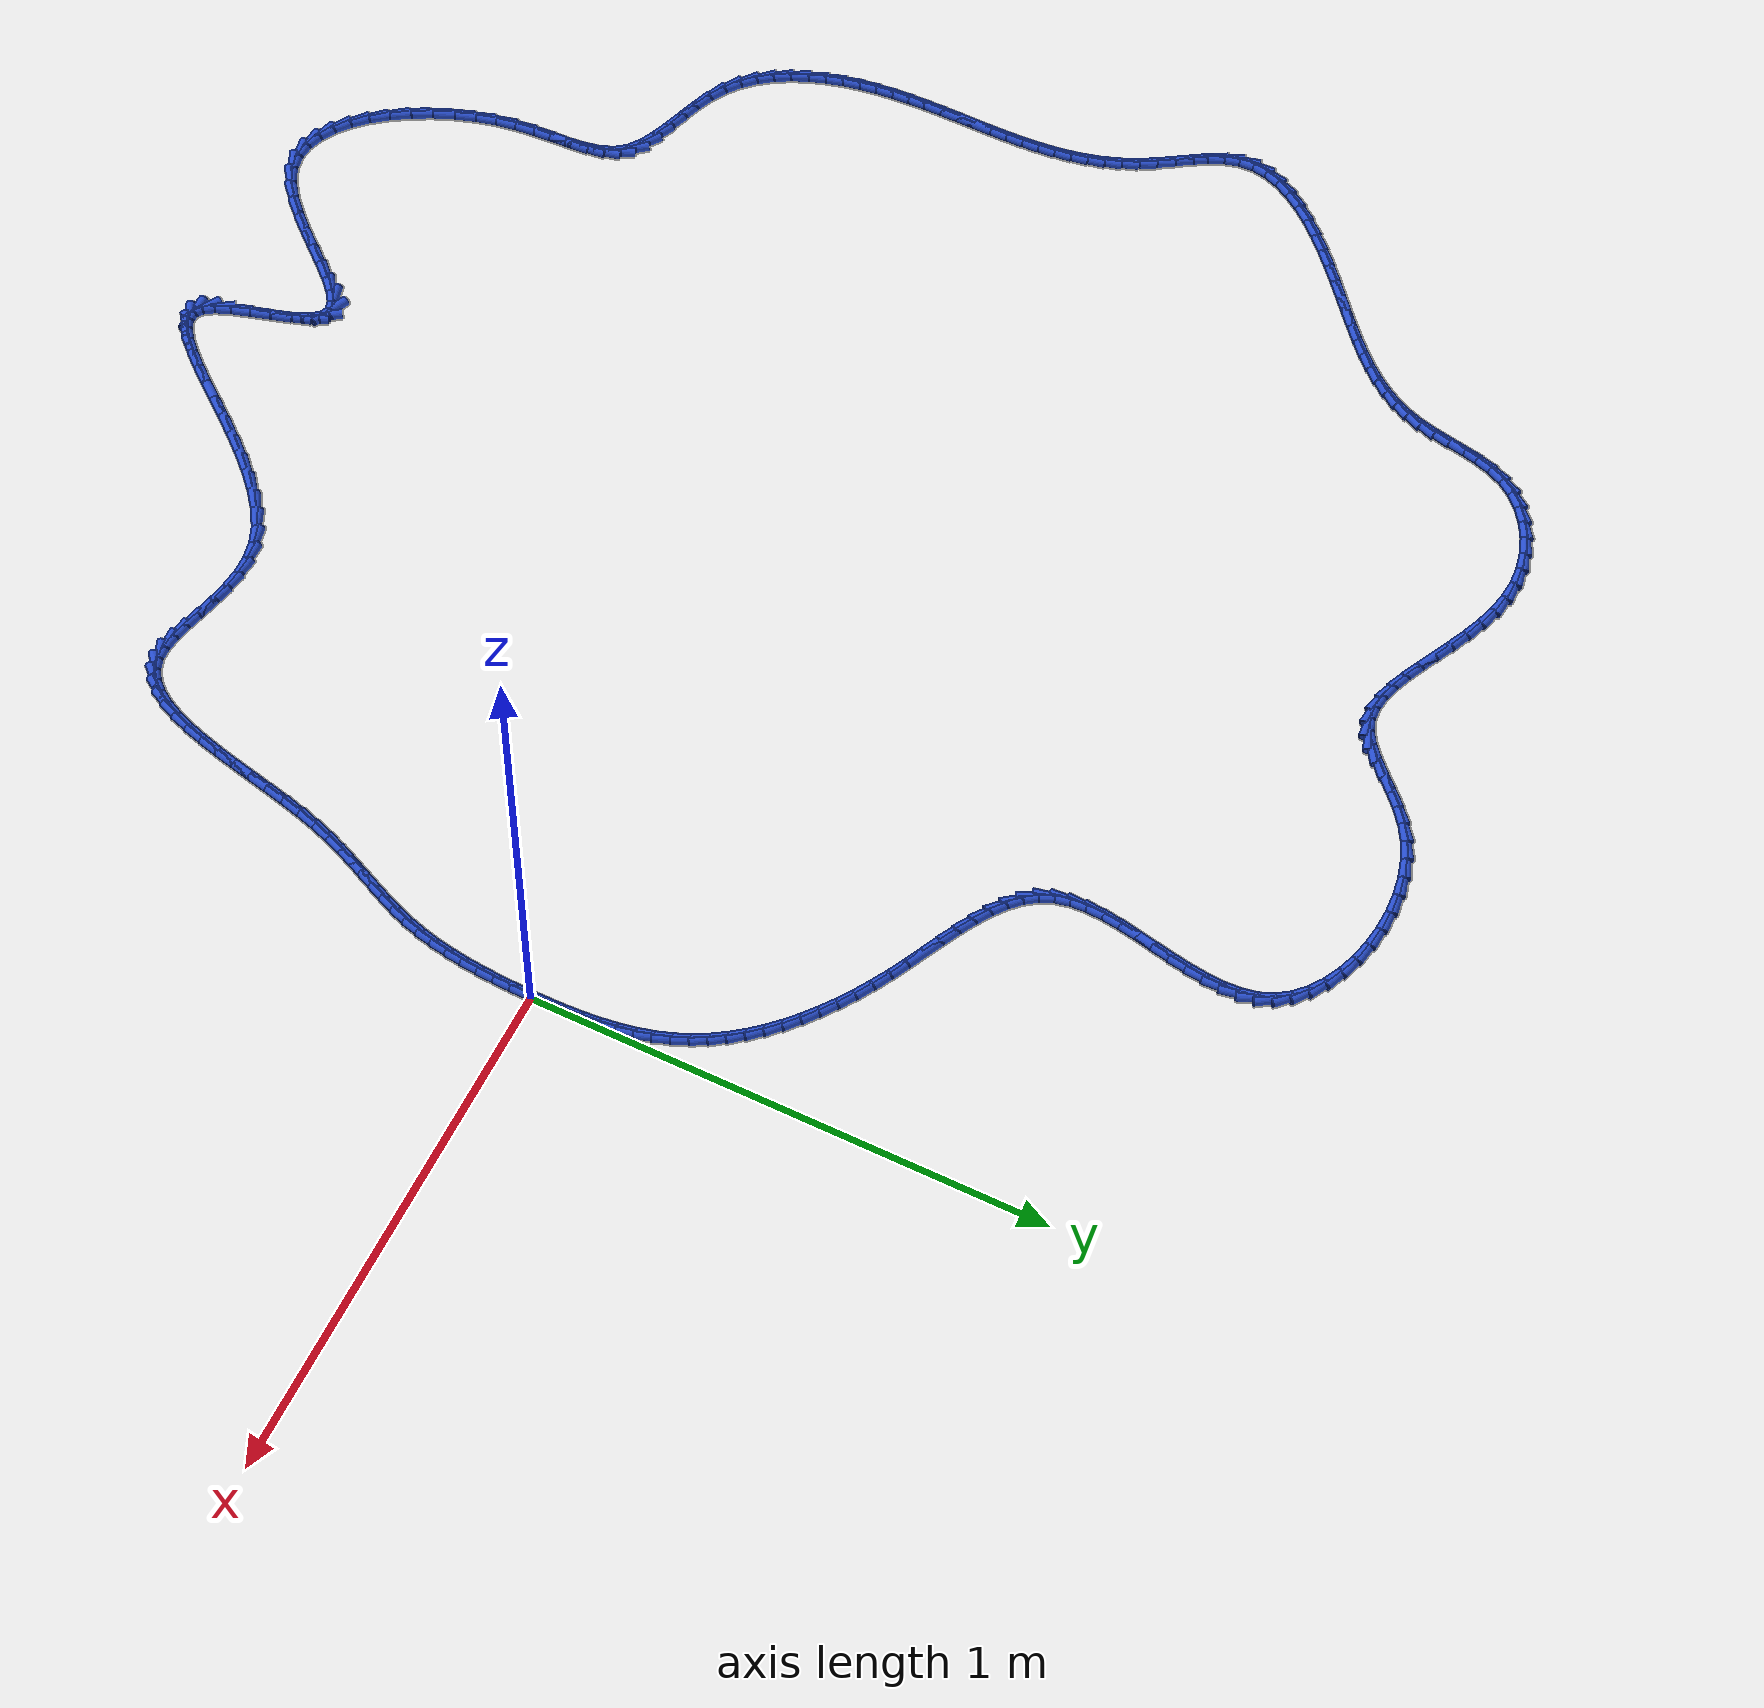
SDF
<sdf version="1.6">
 <world name="default">
  <light name="sun" type="directional">
   <pose>0 0 10 0 -0 0</pose>
   <diffuse>0.8 0.8 0.8 1</diffuse>
   <specular>0.2 0.2 0.2 1</specular>
   <attenuation>
    <range>1000</range>
    <constant>0.9</constant>
    <linear>0.01</linear>
    <quadratic>0.001</quadratic>
   </attenuation>
   <direction>-0.5 0.1 -0.9</direction>
  </light>
  <model name="ground_plane">
   <static>1</static>
   <link name="link">
    <collision name="collision">
     <geometry><plane><normal>0 0 1</normal><size>100 100</size></plane></geometry>
     <surface><friction><ode><mu>100</mu><mu2>50</mu2></ode></friction></surface>
    </collision>
    <visual name="visual">
     <cast_shadows>0</cast_shadows>
     <geometry><plane><normal>0 0 1</normal><size>100 100</size></plane></geometry>
     <material>
      <script><uri>file://media/materials/scripts/gazebo.material</uri><name>Gazebo/WhiteGlow</name></script>
     </material>
    </visual>
   </link>
  </model>
  <gravity>0 0 -9.8</gravity>
  <magnetic_field>6e-06 2.3e-05 -4.2e-05</magnetic_field>
  <atmosphere type="adiabatic"/>
  <physics name="default_physics" default="0" type="ode">
   <max_step_size>0.001</max_step_size>
   <real_time_factor>1</real_time_factor>
   <real_time_update_rate>1000</real_time_update_rate>
  </physics>
  <scene><ambient>0.4 0.4 0.4 1</ambient><background>0.7 0.7 0.7 1</background><shadows>1</shadows></scene>
  <spherical_coordinates>
   <surface_model>EARTH_WGS84</surface_model>
   <latitude_deg>0</latitude_deg>
   <longitude_deg>0</longitude_deg>
   <elevation>0</elevation>
   <heading_deg>0</heading_deg>
  </spherical_coordinates>
  <model name="line">
   <link name="link_0">
    <pose>1.3010426069826053e-18 6.938893903907228e-18 0.01 0 1.57 1.5681028280128086</pose>
    <collision name="collision">
     <geometry><cylinder><radius>0.01</radius><length>0.08</length></cylinder></geometry>
    </collision>
    <visual name="visual">
     <material>
      <script><name>Gazebo/Blue</name><uri>file://media/materials/scripts/gazebo.material</uri></script>
     </material>
     <geometry><cylinder><radius>0.01</radius><length>0.08</length></cylinder></geometry>
    </visual>
   </link>
   <link name="link_1">
    <pose>9.21472946045387e-05 0.03421092015200379 0.01 0 1.57 -1.5492088396381607</pose>
    <collision name="collision">
     <geometry><cylinder><radius>0.01</radius><length>0.08</length></cylinder></geometry>
    </collision>
    <visual name="visual">
     <material>
      <script><name>Gazebo/Blue</name><uri>file://media/materials/scripts/gazebo.material</uri></script>
     </material>
     <geometry><cylinder><radius>0.01</radius><length>0.08</length></cylinder></geometry>
    </visual>
   </link>
   <link name="link_2">
    <pose>-0.00064412734055062 0.06831216840997371 0.01 0 1.57 -1.5178051882876995</pose>
    <collision name="collision">
     <geometry><cylinder><radius>0.01</radius><length>0.08</length></cylinder></geometry>
    </collision>
    <visual name="visual">
     <material>
      <script><name>Gazebo/Blue</name><uri>file://media/materials/scripts/gazebo.material</uri></script>
     </material>
     <geometry><cylinder><radius>0.01</radius><length>0.08</length></cylinder></geometry>
    </visual>
   </link>
   <link name="link_3">
    <pose>-0.002438990591156166 0.10215146603923764 0.01 0 1.57 -1.4788020552186834</pose>
    <collision name="collision">
     <geometry><cylinder><radius>0.01</radius><length>0.08</length></cylinder></geometry>
    </collision>
    <visual name="visual">
     <material>
      <script><name>Gazebo/Blue</name><uri>file://media/materials/scripts/gazebo.material</uri></script>
     </material>
     <geometry><cylinder><radius>0.01</radius><length>0.08</length></cylinder></geometry>
    </visual>
   </link>
   <link name="link_4">
    <pose>-0.005522609142902789 0.1355765343051234 0.01 0 1.57 -1.431630477514693</pose>
    <collision name="collision">
     <geometry><cylinder><radius>0.01</radius><length>0.08</length></cylinder></geometry>
    </collision>
    <visual name="visual">
     <material>
      <script><name>Gazebo/Blue</name><uri>file://media/materials/scripts/gazebo.material</uri></script>
     </material>
     <geometry><cylinder><radius>0.01</radius><length>0.08</length></cylinder></geometry>
    </visual>
   </link>
   <link name="link_5">
    <pose>-0.010125149681481184 0.1684350944729589 0.01 0 1.57 -1.3756852654955114</pose>
    <collision name="collision">
     <geometry><cylinder><radius>0.01</radius><length>0.08</length></cylinder></geometry>
    </collision>
    <visual name="visual">
     <material>
      <script><name>Gazebo/Blue</name><uri>file://media/materials/scripts/gazebo.material</uri></script>
     </material>
     <geometry><cylinder><radius>0.01</radius><length>0.08</length></cylinder></geometry>
    </visual>
   </link>
   <link name="link_6">
    <pose>-0.016476778892582047 0.20057486780807193 0.01 0 1.57 -1.3104160144874581</pose>
    <collision name="collision">
     <geometry><cylinder><radius>0.01</radius><length>0.08</length></cylinder></geometry>
    </collision>
    <visual name="visual">
     <material>
      <script><name>Gazebo/Blue</name><uri>file://media/materials/scripts/gazebo.material</uri></script>
     </material>
     <geometry><cylinder><radius>0.01</radius><length>0.08</length></cylinder></geometry>
    </visual>
   </link>
   <link name="link_7">
    <pose>-0.02480766346189605 0.23184357557579025 0.01 0 1.57 -1.2354670256560256</pose>
    <collision name="collision">
     <geometry><cylinder><radius>0.01</radius><length>0.08</length></cylinder></geometry>
    </collision>
    <visual name="visual">
     <material>
      <script><name>Gazebo/Blue</name><uri>file://media/materials/scripts/gazebo.material</uri></script>
     </material>
     <geometry><cylinder><radius>0.01</radius><length>0.08</length></cylinder></geometry>
    </visual>
   </link>
   <link name="link_8">
    <pose>-0.03534789462071178 0.26208897743912496 0.01 0 1.57 -1.1535806220860858</pose>
    <collision name="collision">
     <geometry><cylinder><radius>0.01</radius><length>0.08</length></cylinder></geometry>
    </collision>
    <visual name="visual">
     <material>
      <script><name>Gazebo/Blue</name><uri>file://media/materials/scripts/gazebo.material</uri></script>
     </material>
     <geometry><cylinder><radius>0.01</radius><length>0.08</length></cylinder></geometry>
    </visual>
   </link>
   <link name="link_9">
    <pose>-0.04825018677093553 0.29119820904033267 0.01 0 1.57 -1.0732351427596591</pose>
    <collision name="collision">
     <geometry><cylinder><radius>0.01</radius><length>0.08</length></cylinder></geometry>
    </collision>
    <visual name="visual">
     <material>
      <script><name>Gazebo/Blue</name><uri>file://media/materials/scripts/gazebo.material</uri></script>
     </material>
     <geometry><cylinder><radius>0.01</radius><length>0.08</length></cylinder></geometry>
    </visual>
   </link>
   <link name="link_10">
    <pose>-0.06344390718443564 0.31917206423210837 0.01 0 1.57 -0.9966311915711461</pose>
    <collision name="collision">
     <geometry><cylinder><radius>0.01</radius><length>0.08</length></cylinder></geometry>
    </collision>
    <visual name="visual">
     <material>
      <script><name>Gazebo/Blue</name><uri>file://media/materials/scripts/gazebo.material</uri></script>
     </material>
     <geometry><cylinder><radius>0.01</radius><length>0.08</length></cylinder></geometry>
    </visual>
   </link>
   <link name="link_11">
    <pose>-0.08081836350786925 0.34603172264650145 0.01 0 1.57 -0.9243331726295042</pose>
    <collision name="collision">
     <geometry><cylinder><radius>0.01</radius><length>0.08</length></cylinder></geometry>
    </collision>
    <visual name="visual">
     <material>
      <script><name>Gazebo/Blue</name><uri>file://media/materials/scripts/gazebo.material</uri></script>
     </material>
     <geometry><cylinder><radius>0.01</radius><length>0.08</length></cylinder></geometry>
    </visual>
   </link>
   <link name="link_12">
    <pose>-0.10026286338789353 0.37179836391556115 0.01 0 1.57 -0.8566665985663992</pose>
    <collision name="collision">
     <geometry><cylinder><radius>0.01</radius><length>0.08</length></cylinder></geometry>
    </collision>
    <visual name="visual">
     <material>
      <script><name>Gazebo/Blue</name><uri>file://media/materials/scripts/gazebo.material</uri></script>
     </material>
     <geometry><cylinder><radius>0.01</radius><length>0.08</length></cylinder></geometry>
    </visual>
   </link>
   <link name="link_13">
    <pose>-0.12166671447116557 0.39649316767133636 0.01 0 1.57 -0.7937490112517714</pose>
    <collision name="collision">
     <geometry><cylinder><radius>0.01</radius><length>0.08</length></cylinder></geometry>
    </collision>
    <visual name="visual">
     <material>
      <script><name>Gazebo/Blue</name><uri>file://media/materials/scripts/gazebo.material</uri></script>
     </material>
     <geometry><cylinder><radius>0.01</radius><length>0.08</length></cylinder></geometry>
    </visual>
   </link>
   <link name="link_14">
    <pose>-0.14491922440434257 0.42013731354587663 0.01 0 1.57 -0.7355329787320553</pose>
    <collision name="collision">
     <geometry><cylinder><radius>0.01</radius><length>0.08</length></cylinder></geometry>
    </collision>
    <visual name="visual">
     <material>
      <script><name>Gazebo/Blue</name><uri>file://media/materials/scripts/gazebo.material</uri></script>
     </material>
     <geometry><cylinder><radius>0.01</radius><length>0.08</length></cylinder></geometry>
    </visual>
   </link>
   <link name="link_15">
    <pose>-0.16990970083408158 0.4427519811712309 0.01 0 1.57 -0.6818512623761129</pose>
    <collision name="collision">
     <geometry><cylinder><radius>0.01</radius><length>0.08</length></cylinder></geometry>
    </collision>
    <visual name="visual">
     <material>
      <script><name>Gazebo/Blue</name><uri>file://media/materials/scripts/gazebo.material</uri></script>
     </material>
     <geometry><cylinder><radius>0.01</radius><length>0.08</length></cylinder></geometry>
    </visual>
   </link>
   <link name="link_16">
    <pose>-0.19652745140703984 0.4643583501794485 0.01 0 1.57 -0.6324576854109352</pose>
    <collision name="collision">
     <geometry><cylinder><radius>0.01</radius><length>0.08</length></cylinder></geometry>
    </collision>
    <visual name="visual">
     <material>
      <script><name>Gazebo/Blue</name><uri>file://media/materials/scripts/gazebo.material</uri></script>
     </material>
     <geometry><cylinder><radius>0.01</radius><length>0.08</length></cylinder></geometry>
    </visual>
   </link>
   <link name="link_17">
    <pose>-0.2246617837698745 0.4849776002025788 0.01 0 1.57 -0.5870605718990818</pose>
    <collision name="collision">
     <geometry><cylinder><radius>0.01</radius><length>0.08</length></cylinder></geometry>
    </collision>
    <visual name="visual">
     <material>
      <script><name>Gazebo/Blue</name><uri>file://media/materials/scripts/gazebo.material</uri></script>
     </material>
     <geometry><cylinder><radius>0.01</radius><length>0.08</length></cylinder></geometry>
    </visual>
   </link>
   <link name="link_18">
    <pose>-0.2542020055692426 0.5046309108726706 0.01 0 1.57 -0.5453480602580567</pose>
    <collision name="collision">
     <geometry><cylinder><radius>0.01</radius><length>0.08</length></cylinder></geometry>
    </collision>
    <visual name="visual">
     <material>
      <script><name>Gazebo/Blue</name><uri>file://media/materials/scripts/gazebo.material</uri></script>
     </material>
     <geometry><cylinder><radius>0.01</radius><length>0.08</length></cylinder></geometry>
    </visual>
   </link>
   <link name="link_19">
    <pose>-0.28503742445180136 0.5233394618217735 0.01 0 1.57 -0.5070060092052388</pose>
    <collision name="collision">
     <geometry><cylinder><radius>0.01</radius><length>0.08</length></cylinder></geometry>
    </collision>
    <visual name="visual">
     <material>
      <script><name>Gazebo/Blue</name><uri>file://media/materials/scripts/gazebo.material</uri></script>
     </material>
     <geometry><cylinder><radius>0.01</radius><length>0.08</length></cylinder></geometry>
    </visual>
   </link>
   <link name="link_20">
    <pose>-0.31705734806420793 0.5411244326819367 0.01 0 1.57 -0.4723065836649267</pose>
    <collision name="collision">
     <geometry><cylinder><radius>0.01</radius><length>0.08</length></cylinder></geometry>
    </collision>
    <visual name="visual">
     <material>
      <script><name>Gazebo/Blue</name><uri>file://media/materials/scripts/gazebo.material</uri></script>
     </material>
     <geometry><cylinder><radius>0.01</radius><length>0.08</length></cylinder></geometry>
    </visual>
   </link>
   <link name="link_21">
    <pose>-0.35012993645930496 0.558020260844207 0.01 0 1.57 -0.44979225682347584</pose>
    <collision name="collision">
     <geometry><cylinder><radius>0.01</radius><length>0.08</length></cylinder></geometry>
    </collision>
    <visual name="visual">
     <material>
      <script><name>Gazebo/Blue</name><uri>file://media/materials/scripts/gazebo.material</uri></script>
     </material>
     <geometry><cylinder><radius>0.01</radius><length>0.08</length></cylinder></geometry>
    </visual>
   </link>
   <link name="link_22">
    <pose>-0.38378915678963865 0.5742708944822692 0.01 0 1.57 -0.4458269354989486</pose>
    <collision name="collision">
     <geometry><cylinder><radius>0.01</radius><length>0.08</length></cylinder></geometry>
    </collision>
    <visual name="visual">
     <material>
      <script><name>Gazebo/Blue</name><uri>file://media/materials/scripts/gazebo.material</uri></script>
     </material>
     <geometry><cylinder><radius>0.01</radius><length>0.08</length></cylinder></geometry>
    </visual>
   </link>
   <link name="link_23">
    <pose>-0.4173023155656656 0.5902874555181831 0.01 0 1.57 -0.46081837163876044</pose>
    <collision name="collision">
     <geometry><cylinder><radius>0.01</radius><length>0.08</length></cylinder></geometry>
    </collision>
    <visual name="visual">
     <material>
      <script><name>Gazebo/Blue</name><uri>file://media/materials/scripts/gazebo.material</uri></script>
     </material>
     <geometry><cylinder><radius>0.01</radius><length>0.08</length></cylinder></geometry>
    </visual>
   </link>
   <link name="link_24">
    <pose>-0.4499292942820158 0.6064857207331493 0.01 0 1.57 -0.4965153031194417</pose>
    <collision name="collision">
     <geometry><cylinder><radius>0.01</radius><length>0.08</length></cylinder></geometry>
    </collision>
    <visual name="visual">
     <material>
      <script><name>Gazebo/Blue</name><uri>file://media/materials/scripts/gazebo.material</uri></script>
     </material>
     <geometry><cylinder><radius>0.01</radius><length>0.08</length></cylinder></geometry>
    </visual>
   </link>
   <link name="link_25">
    <pose>-0.48092997443331903 0.6232814669083686 0.01 0 1.57 -0.5564011358206382</pose>
    <collision name="collision">
     <geometry><cylinder><radius>0.01</radius><length>0.08</length></cylinder></geometry>
    </collision>
    <visual name="visual">
     <material>
      <script><name>Gazebo/Blue</name><uri>file://media/materials/scripts/gazebo.material</uri></script>
     </material>
     <geometry><cylinder><radius>0.01</radius><length>0.08</length></cylinder></geometry>
    </visual>
   </link>
   <link name="link_26">
    <pose>-0.5095642375142055 0.6410904708250419 0.01 0 1.57 -0.6458096996146597</pose>
    <collision name="collision">
     <geometry><cylinder><radius>0.01</radius><length>0.08</length></cylinder></geometry>
    </collision>
    <visual name="visual">
     <material>
      <script><name>Gazebo/Blue</name><uri>file://media/materials/scripts/gazebo.material</uri></script>
     </material>
     <geometry><cylinder><radius>0.01</radius><length>0.08</length></cylinder></geometry>
    </visual>
   </link>
   <link name="link_27">
    <pose>-0.5350919650193056 0.6603285092643697 0.01 0 1.57 -0.7714100954514999</pose>
    <collision name="collision">
     <geometry><cylinder><radius>0.01</radius><length>0.08</length></cylinder></geometry>
    </collision>
    <visual name="visual">
     <material>
      <script><name>Gazebo/Blue</name><uri>file://media/materials/scripts/gazebo.material</uri></script>
     </material>
     <geometry><cylinder><radius>0.01</radius><length>0.08</length></cylinder></geometry>
    </visual>
   </link>
   <link name="link_28">
    <pose>-0.5567730384432488 0.681411359007553 0.01 0 1.57 -0.9387225401074779</pose>
    <collision name="collision">
     <geometry><cylinder><radius>0.01</radius><length>0.08</length></cylinder></geometry>
    </collision>
    <visual name="visual">
     <material>
      <script><name>Gazebo/Blue</name><uri>file://media/materials/scripts/gazebo.material</uri></script>
     </material>
     <geometry><cylinder><radius>0.01</radius><length>0.08</length></cylinder></geometry>
    </visual>
   </link>
   <link name="link_29">
    <pose>-0.5738673392806655 0.7047547968357923 0.01 0 1.57 -1.14550184339439</pose>
    <collision name="collision">
     <geometry><cylinder><radius>0.01</radius><length>0.08</length></cylinder></geometry>
    </collision>
    <visual name="visual">
     <material>
      <script><name>Gazebo/Blue</name><uri>file://media/materials/scripts/gazebo.material</uri></script>
     </material>
     <geometry><cylinder><radius>0.01</radius><length>0.08</length></cylinder></geometry>
    </visual>
   </link>
   <link name="link_30">
    <pose>-0.5856492868402612 0.7307670711242708 0.01 0 1.57 -1.351774952093321</pose>
    <collision name="collision">
     <geometry><cylinder><radius>0.01</radius><length>0.08</length></cylinder></geometry>
    </collision>
    <visual name="visual">
     <material>
      <script><name>Gazebo/Blue</name><uri>file://media/materials/scripts/gazebo.material</uri></script>
     </material>
     <geometry><cylinder><radius>0.01</radius><length>0.08</length></cylinder></geometry>
    </visual>
   </link>
   <link name="link_31">
    <pose>-0.5920487900779455 0.7595169849794902 0.01 0 1.57 -1.5112019829685073</pose>
    <collision name="collision">
     <geometry><cylinder><radius>0.01</radius><length>0.08</length></cylinder></geometry>
    </collision>
    <visual name="visual">
     <material>
      <script><name>Gazebo/Blue</name><uri>file://media/materials/scripts/gazebo.material</uri></script>
     </material>
     <geometry><cylinder><radius>0.01</radius><length>0.08</length></cylinder></geometry>
    </visual>
   </link>
   <link name="link_32">
    <pose>-0.5939035513330879 0.7906032407668235 0.01 0 1.57 1.5167184158288343</pose>
    <collision name="collision">
     <geometry><cylinder><radius>0.01</radius><length>0.08</length></cylinder></geometry>
    </collision>
    <visual name="visual">
     <material>
      <script><name>Gazebo/Blue</name><uri>file://media/materials/scripts/gazebo.material</uri></script>
     </material>
     <geometry><cylinder><radius>0.01</radius><length>0.08</length></cylinder></geometry>
    </visual>
   </link>
   <link name="link_33">
    <pose>-0.5921179548317503 0.8235900096412082 0.01 0 1.57 1.440297520970659</pose>
    <collision name="collision">
     <geometry><cylinder><radius>0.01</radius><length>0.08</length></cylinder></geometry>
    </collision>
    <visual name="visual">
     <material>
      <script><name>Gazebo/Blue</name><uri>file://media/materials/scripts/gazebo.material</uri></script>
     </material>
     <geometry><cylinder><radius>0.01</radius><length>0.08</length></cylinder></geometry>
    </visual>
   </link>
   <link name="link_34">
    <pose>-0.5875963847999945 0.8580414627575832 0.01 0 1.57 1.3936125273458404</pose>
    <collision name="collision">
     <geometry><cylinder><radius>0.01</radius><length>0.08</length></cylinder></geometry>
    </collision>
    <visual name="visual">
     <material>
      <script><name>Gazebo/Blue</name><uri>file://media/materials/scripts/gazebo.material</uri></script>
     </material>
     <geometry><cylinder><radius>0.01</radius><length>0.08</length></cylinder></geometry>
    </visual>
   </link>
   <link name="link_35">
    <pose>-0.5812432254638826 0.8935217712708868 0.01 0 1.57 1.3716502108383468</pose>
    <collision name="collision">
     <geometry><cylinder><radius>0.01</radius><length>0.08</length></cylinder></geometry>
    </collision>
    <visual name="visual">
     <material>
      <script><name>Gazebo/Blue</name><uri>file://media/materials/scripts/gazebo.material</uri></script>
     </material>
     <geometry><cylinder><radius>0.01</radius><length>0.08</length></cylinder></geometry>
    </visual>
   </link>
   <link name="link_36">
    <pose>-0.5739628610494766 0.9295951063360577 0.01 0 1.57 1.3718863892041935</pose>
    <collision name="collision">
     <geometry><cylinder><radius>0.01</radius><length>0.08</length></cylinder></geometry>
    </collision>
    <visual name="visual">
     <material>
      <script><name>Gazebo/Blue</name><uri>file://media/materials/scripts/gazebo.material</uri></script>
     </material>
     <geometry><cylinder><radius>0.01</radius><length>0.08</length></cylinder></geometry>
    </visual>
   </link>
   <link name="link_37">
    <pose>-0.5666596757828386 0.9658256391080344 0.01 0 1.57 1.3940432788324997</pose>
    <collision name="collision">
     <geometry><cylinder><radius>0.01</radius><length>0.08</length></cylinder></geometry>
    </collision>
    <visual name="visual">
     <material>
      <script><name>Gazebo/Blue</name><uri>file://media/materials/scripts/gazebo.material</uri></script>
     </material>
     <geometry><cylinder><radius>0.01</radius><length>0.08</length></cylinder></geometry>
    </visual>
   </link>
   <link name="link_38">
    <pose>-0.5602380538900305 1.0017775407417546 0.01 0 1.57 1.4399921175468742</pose>
    <collision name="collision">
     <geometry><cylinder><radius>0.01</radius><length>0.08</length></cylinder></geometry>
    </collision>
    <visual name="visual">
     <material>
      <script><name>Gazebo/Blue</name><uri>file://media/materials/scripts/gazebo.material</uri></script>
     </material>
     <geometry><cylinder><radius>0.01</radius><length>0.08</length></cylinder></geometry>
    </visual>
   </link>
   <link name="link_39">
    <pose>-0.555602379597114 1.037014982392158 0.01 0 1.57 1.5137884964370198</pose>
    <collision name="collision">
     <geometry><cylinder><radius>0.01</radius><length>0.08</length></cylinder></geometry>
    </collision>
    <visual name="visual">
     <material>
      <script><name>Gazebo/Blue</name><uri>file://media/materials/scripts/gazebo.material</uri></script>
     </material>
     <geometry><cylinder><radius>0.01</radius><length>0.08</length></cylinder></geometry>
    </visual>
   </link>
   <link name="link_40">
    <pose>-0.5536570371301516 1.071102135214182 0.01 0 1.57 -1.520091485164762</pose>
    <collision name="collision">
     <geometry><cylinder><radius>0.01</radius><length>0.08</length></cylinder></geometry>
    </collision>
    <visual name="visual">
     <material>
      <script><name>Gazebo/Blue</name><uri>file://media/materials/scripts/gazebo.material</uri></script>
     </material>
     <geometry><cylinder><radius>0.01</radius><length>0.08</length></cylinder></geometry>
    </visual>
   </link>
   <link name="link_41">
    <pose>-0.5553064107152048 1.1036031703627656 0.01 0 1.57 -1.371740151712836</pose>
    <collision name="collision">
     <geometry><cylinder><radius>0.01</radius><length>0.08</length></cylinder></geometry>
    </collision>
    <visual name="visual">
     <material>
      <script><name>Gazebo/Blue</name><uri>file://media/materials/scripts/gazebo.material</uri></script>
     </material>
     <geometry><cylinder><radius>0.01</radius><length>0.08</length></cylinder></geometry>
    </visual>
   </link>
   <link name="link_42">
    <pose>-0.5614548845783358 1.134082258992847 0.01 0 1.57 -1.1798031312042947</pose>
    <collision name="collision">
     <geometry><cylinder><radius>0.01</radius><length>0.08</length></cylinder></geometry>
    </collision>
    <visual name="visual">
     <material>
      <script><name>Gazebo/Blue</name><uri>file://media/materials/scripts/gazebo.material</uri></script>
     </material>
     <geometry><cylinder><radius>0.01</radius><length>0.08</length></cylinder></geometry>
    </visual>
   </link>
   <link name="link_43">
    <pose>-0.5730058081417366 1.1621037630248632 0.01 0 1.57 -0.9656473261107855</pose>
    <collision name="collision">
     <geometry><cylinder><radius>0.01</radius><length>0.08</length></cylinder></geometry>
    </collision>
    <visual name="visual">
     <material>
      <script><name>Gazebo/Blue</name><uri>file://media/materials/scripts/gazebo.material</uri></script>
     </material>
     <geometry><cylinder><radius>0.01</radius><length>0.08</length></cylinder></geometry>
    </visual>
   </link>
   <link name="link_44">
    <pose>-0.5904413193748509 1.1873096944682136 0.01 0 1.57 -0.7741221120359179</pose>
    <collision name="collision">
     <geometry><cylinder><radius>0.01</radius><length>0.08</length></cylinder></geometry>
    </collision>
    <visual name="visual">
     <material>
      <script><name>Gazebo/Blue</name><uri>file://media/materials/scripts/gazebo.material</uri></script>
     </material>
     <geometry><cylinder><radius>0.01</radius><length>0.08</length></cylinder></geometry>
    </visual>
   </link>
   <link name="link_45">
    <pose>-0.6131773018282735 1.2095386287209282 0.01 0 1.57 -0.6112378195390655</pose>
    <collision name="collision">
     <geometry><cylinder><radius>0.01</radius><length>0.08</length></cylinder></geometry>
    </collision>
    <visual name="visual">
     <material>
      <script><name>Gazebo/Blue</name><uri>file://media/materials/scripts/gazebo.material</uri></script>
     </material>
     <geometry><cylinder><radius>0.01</radius><length>0.08</length></cylinder></geometry>
    </visual>
   </link>
   <link name="link_46">
    <pose>-0.6404634815979583 1.2286597722121977 0.01 0 1.57 -0.4723466039167732</pose>
    <collision name="collision">
     <geometry><cylinder><radius>0.01</radius><length>0.08</length></cylinder></geometry>
    </collision>
    <visual name="visual">
     <material>
      <script><name>Gazebo/Blue</name><uri>file://media/materials/scripts/gazebo.material</uri></script>
     </material>
     <geometry><cylinder><radius>0.01</radius><length>0.08</length></cylinder></geometry>
    </visual>
   </link>
   <link name="link_47">
    <pose>-0.6715495847798604 1.2445423313712138 0.01 0 1.57 -0.3513605722321595</pose>
    <collision name="collision">
     <geometry><cylinder><radius>0.01</radius><length>0.08</length></cylinder></geometry>
    </collision>
    <visual name="visual">
     <material>
      <script><name>Gazebo/Blue</name><uri>file://media/materials/scripts/gazebo.material</uri></script>
     </material>
     <geometry><cylinder><radius>0.01</radius><length>0.08</length></cylinder></geometry>
    </visual>
   </link>
   <link name="link_48">
    <pose>-0.7056853374699339 1.257055512627167 0.01 0 1.57 -0.24250318873358515</pose>
    <collision name="collision">
     <geometry><cylinder><radius>0.01</radius><length>0.08</length></cylinder></geometry>
    </collision>
    <visual name="visual">
     <material>
      <script><name>Gazebo/Blue</name><uri>file://media/materials/scripts/gazebo.material</uri></script>
     </material>
     <geometry><cylinder><radius>0.01</radius><length>0.08</length></cylinder></geometry>
    </visual>
   </link>
   <link name="link_49">
    <pose>-0.742120465764133 1.266068522409248 0.01 0 1.57 -0.14075459577268148</pose>
    <collision name="collision">
     <geometry><cylinder><radius>0.01</radius><length>0.08</length></cylinder></geometry>
    </collision>
    <visual name="visual">
     <material>
      <script><name>Gazebo/Blue</name><uri>file://media/materials/scripts/gazebo.material</uri></script>
     </material>
     <geometry><cylinder><radius>0.01</radius><length>0.08</length></cylinder></geometry>
    </visual>
   </link>
   <link name="link_50">
    <pose>-0.7801046957584133 1.2714505671466487 0.01 0 1.57 -0.04175391287469112</pose>
    <collision name="collision">
     <geometry><cylinder><radius>0.01</radius><length>0.08</length></cylinder></geometry>
    </collision>
    <visual name="visual">
     <material>
      <script><name>Gazebo/Blue</name><uri>file://media/materials/scripts/gazebo.material</uri></script>
     </material>
     <geometry><cylinder><radius>0.01</radius><length>0.08</length></cylinder></geometry>
    </visual>
   </link>
   <link name="link_51">
    <pose>-0.8188877535487284 1.2730708532685595 0.01 0 1.57 0.058449232108458066</pose>
    <collision name="collision">
     <geometry><cylinder><radius>0.01</radius><length>0.08</length></cylinder></geometry>
    </collision>
    <visual name="visual">
     <material>
      <script><name>Gazebo/Blue</name><uri>file://media/materials/scripts/gazebo.material</uri></script>
     </material>
     <geometry><cylinder><radius>0.01</radius><length>0.08</length></cylinder></geometry>
    </visual>
   </link>
   <link name="link_52">
    <pose>-0.8577193652310333 1.2707985872041716 0.01 0 1.57 0.16363332900906782</pose>
    <collision name="collision">
     <geometry><cylinder><radius>0.01</radius><length>0.08</length></cylinder></geometry>
    </collision>
    <visual name="visual">
     <material>
      <script><name>Gazebo/Blue</name><uri>file://media/materials/scripts/gazebo.material</uri></script>
     </material>
     <geometry><cylinder><radius>0.01</radius><length>0.08</length></cylinder></geometry>
    </visual>
   </link>
   <link name="link_53">
    <pose>-0.8958492569012824 1.2645029753826762 0.01 0 1.57 0.2775521664038082</pose>
    <collision name="collision">
     <geometry><cylinder><radius>0.01</radius><length>0.08</length></cylinder></geometry>
    </collision>
    <visual name="visual">
     <material>
      <script><name>Gazebo/Blue</name><uri>file://media/materials/scripts/gazebo.material</uri></script>
     </material>
     <geometry><cylinder><radius>0.01</radius><length>0.08</length></cylinder></geometry>
    </visual>
   </link>
   <link name="link_54">
    <pose>-0.9325271546554303 1.254053224233264 0.01 0 1.57 0.40389680177569504</pose>
    <collision name="collision">
     <geometry><cylinder><radius>0.01</radius><length>0.08</length></cylinder></geometry>
    </collision>
    <visual name="visual">
     <material>
      <script><name>Gazebo/Blue</name><uri>file://media/materials/scripts/gazebo.material</uri></script>
     </material>
     <geometry><cylinder><radius>0.01</radius><length>0.08</length></cylinder></geometry>
    </visual>
   </link>
   <link name="link_55">
    <pose>-0.9670027845894313 1.2393185401851263 0.01 0 1.57 0.5445401659723318</pose>
    <collision name="collision">
     <geometry><cylinder><radius>0.01</radius><length>0.08</length></cylinder></geometry>
    </collision>
    <visual name="visual">
     <material>
      <script><name>Gazebo/Blue</name><uri>file://media/materials/scripts/gazebo.material</uri></script>
     </material>
     <geometry><cylinder><radius>0.01</radius><length>0.08</length></cylinder></geometry>
    </visual>
   </link>
   <link name="link_56">
    <pose>-0.9985576978041976 1.2202083158968158 0.01 0 1.57 0.6705837889567258</pose>
    <collision name="collision">
     <geometry><cylinder><radius>0.01</radius><length>0.08</length></cylinder></geometry>
    </collision>
    <visual name="visual">
     <material>
      <script><name>Gazebo/Blue</name><uri>file://media/materials/scripts/gazebo.material</uri></script>
     </material>
     <geometry><cylinder><radius>0.01</radius><length>0.08</length></cylinder></geometry>
    </visual>
   </link>
   <link name="link_57">
    <pose>-1.0271706803305822 1.197512360003284 0.01 0 1.57 0.7521878209823392</pose>
    <collision name="collision">
     <geometry><cylinder><radius>0.01</radius><length>0.08</length></cylinder></geometry>
    </collision>
    <visual name="visual">
     <material>
      <script><name>Gazebo/Blue</name><uri>file://media/materials/scripts/gazebo.material</uri></script>
     </material>
     <geometry><cylinder><radius>0.01</radius><length>0.08</length></cylinder></geometry>
    </visual>
   </link>
   <link name="link_58">
    <pose>-1.0534989823114589 1.1728771947348358 0.01 0 1.57 0.7886924235214735</pose>
    <collision name="collision">
     <geometry><cylinder><radius>0.01</radius><length>0.08</length></cylinder></geometry>
    </collision>
    <visual name="visual">
     <material>
      <script><name>Gazebo/Blue</name><uri>file://media/materials/scripts/gazebo.material</uri></script>
     </material>
     <geometry><cylinder><radius>0.01</radius><length>0.08</length></cylinder></geometry>
    </visual>
   </link>
   <link name="link_59">
    <pose>-1.0782279238545378 1.1479847869681048 0.01 0 1.57 0.7780548342132023</pose>
    <collision name="collision">
     <geometry><cylinder><radius>0.01</radius><length>0.08</length></cylinder></geometry>
    </collision>
    <visual name="visual">
     <material>
      <script><name>Gazebo/Blue</name><uri>file://media/materials/scripts/gazebo.material</uri></script>
     </material>
     <geometry><cylinder><radius>0.01</radius><length>0.08</length></cylinder></geometry>
    </visual>
   </link>
   <link name="link_60">
    <pose>-1.1020428250675303 1.1245171035797252 0.01 0 1.57 0.7121416324963395</pose>
    <collision name="collision">
     <geometry><cylinder><radius>0.01</radius><length>0.08</length></cylinder></geometry>
    </collision>
    <visual name="visual">
     <material>
      <script><name>Gazebo/Blue</name><uri>file://media/materials/scripts/gazebo.material</uri></script>
     </material>
     <geometry><cylinder><radius>0.01</radius><length>0.08</length></cylinder></geometry>
    </visual>
   </link>
   <link name="link_61">
    <pose>-1.1256290060581469 1.1041561114463307 0.01 0 1.57 0.5747515165996864</pose>
    <collision name="collision">
     <geometry><cylinder><radius>0.01</radius><length>0.08</length></cylinder></geometry>
    </collision>
    <visual name="visual">
     <material>
      <script><name>Gazebo/Blue</name><uri>file://media/materials/scripts/gazebo.material</uri></script>
     </material>
     <geometry><cylinder><radius>0.01</radius><length>0.08</length></cylinder></geometry>
    </visual>
   </link>
   <link name="link_62">
    <pose>-1.149671786934099 1.0885837774445564 0.01 0 1.57 0.3488466369928882</pose>
    <collision name="collision">
     <geometry><cylinder><radius>0.01</radius><length>0.08</length></cylinder></geometry>
    </collision>
    <visual name="visual">
     <material>
      <script><name>Gazebo/Blue</name><uri>file://media/materials/scripts/gazebo.material</uri></script>
     </material>
     <geometry><cylinder><radius>0.01</radius><length>0.08</length></cylinder></geometry>
    </visual>
   </link>
   <link name="link_63">
    <pose>-1.174841246288688 1.0794290913362818 0.01 0 1.57 0.0899843176316116</pose>
    <collision name="collision">
     <geometry><cylinder><radius>0.01</radius><length>0.08</length></cylinder></geometry>
    </collision>
    <visual name="visual">
     <material>
      <script><name>Gazebo/Blue</name><uri>file://media/materials/scripts/gazebo.material</uri></script>
     </material>
     <geometry><cylinder><radius>0.01</radius><length>0.08</length></cylinder></geometry>
    </visual>
   </link>
   <link name="link_64">
    <pose>-1.2014358888739824 1.077029510461045 0.01 0 1.57 -0.11968812535510313</pose>
    <collision name="collision">
     <geometry><cylinder><radius>0.01</radius><length>0.08</length></cylinder></geometry>
    </collision>
    <visual name="visual">
     <material>
      <script><name>Gazebo/Blue</name><uri>file://media/materials/scripts/gazebo.material</uri></script>
     </material>
     <geometry><cylinder><radius>0.01</radius><length>0.08</length></cylinder></geometry>
    </visual>
   </link>
   <link name="link_65">
    <pose>-1.2293705790894476 1.0803890184341105 0.01 0 1.57 -0.2696063682310932</pose>
    <collision name="collision">
     <geometry><cylinder><radius>0.01</radius><length>0.08</length></cylinder></geometry>
    </collision>
    <visual name="visual">
     <material>
      <script><name>Gazebo/Blue</name><uri>file://media/materials/scripts/gazebo.material</uri></script>
     </material>
     <geometry><cylinder><radius>0.01</radius><length>0.08</length></cylinder></geometry>
    </visual>
   </link>
   <link name="link_66">
    <pose>-1.2585425257451917 1.0884502308099155 0.01 0 1.57 -0.3685878554628061</pose>
    <collision name="collision">
     <geometry><cylinder><radius>0.01</radius><length>0.08</length></cylinder></geometry>
    </collision>
    <visual name="visual">
     <material>
      <script><name>Gazebo/Blue</name><uri>file://media/materials/scripts/gazebo.material</uri></script>
     </material>
     <geometry><cylinder><radius>0.01</radius><length>0.08</length></cylinder></geometry>
    </visual>
   </link>
   <link name="link_67">
    <pose>-1.288848937651321 1.100155763142898 0.01 0 1.57 -0.427893086260009</pose>
    <collision name="collision">
     <geometry><cylinder><radius>0.01</radius><length>0.08</length></cylinder></geometry>
    </collision>
    <visual name="visual">
     <material>
      <script><name>Gazebo/Blue</name><uri>file://media/materials/scripts/gazebo.material</uri></script>
     </material>
     <geometry><cylinder><radius>0.01</radius><length>0.08</length></cylinder></geometry>
    </visual>
   </link>
   <link name="link_68">
    <pose>-1.3201870236179438 1.1144482309874966 0.01 0 1.57 -0.45589561942420453</pose>
    <collision name="collision">
     <geometry><cylinder><radius>0.01</radius><length>0.08</length></cylinder></geometry>
    </collision>
    <visual name="visual">
     <material>
      <script><name>Gazebo/Blue</name><uri>file://media/materials/scripts/gazebo.material</uri></script>
     </material>
     <geometry><cylinder><radius>0.01</radius><length>0.08</length></cylinder></geometry>
    </visual>
   </link>
   <link name="link_69">
    <pose>-1.3524539924551677 1.1302702498981496 0.01 0 1.57 -0.45752877678386916</pose>
    <collision name="collision">
     <geometry><cylinder><radius>0.01</radius><length>0.08</length></cylinder></geometry>
    </collision>
    <visual name="visual">
     <material>
      <script><name>Gazebo/Blue</name><uri>file://media/materials/scripts/gazebo.material</uri></script>
     </material>
     <geometry><cylinder><radius>0.01</radius><length>0.08</length></cylinder></geometry>
    </visual>
   </link>
   <link name="link_70">
    <pose>-1.3855470529731004 1.1465644354292943 0.01 0 1.57 -0.43487732825436</pose>
    <collision name="collision">
     <geometry><cylinder><radius>0.01</radius><length>0.08</length></cylinder></geometry>
    </collision>
    <visual name="visual">
     <material>
      <script><name>Gazebo/Blue</name><uri>file://media/materials/scripts/gazebo.material</uri></script>
     </material>
     <geometry><cylinder><radius>0.01</radius><length>0.08</length></cylinder></geometry>
    </visual>
   </link>
   <link name="link_71">
    <pose>-1.4193634139818494 1.1622734031353688 0.01 0 1.57 -0.38778514131040825</pose>
    <collision name="collision">
     <geometry><cylinder><radius>0.01</radius><length>0.08</length></cylinder></geometry>
    </collision>
    <visual name="visual">
     <material>
      <script><name>Gazebo/Blue</name><uri>file://media/materials/scripts/gazebo.material</uri></script>
     </material>
     <geometry><cylinder><radius>0.01</radius><length>0.08</length></cylinder></geometry>
    </visual>
   </link>
   <link name="link_72">
    <pose>-1.4538002842915223 1.1763397685708115 0.01 0 1.57 -0.31439070102544975</pose>
    <collision name="collision">
     <geometry><cylinder><radius>0.01</radius><length>0.08</length></cylinder></geometry>
    </collision>
    <visual name="visual">
     <material>
      <script><name>Gazebo/Blue</name><uri>file://media/materials/scripts/gazebo.material</uri></script>
     </material>
     <geometry><cylinder><radius>0.01</radius><length>0.08</length></cylinder></geometry>
    </visual>
   </link>
   <link name="link_73">
    <pose>-1.4887548727122262 1.18770614729006 0.01 0 1.57 -0.21189943263879663</pose>
    <collision name="collision">
     <geometry><cylinder><radius>0.01</radius><length>0.08</length></cylinder></geometry>
    </collision>
    <visual name="visual">
     <material>
      <script><name>Gazebo/Blue</name><uri>file://media/materials/scripts/gazebo.material</uri></script>
     </material>
     <geometry><cylinder><radius>0.01</radius><length>0.08</length></cylinder></geometry>
    </visual>
   </link>
   <link name="link_74">
    <pose>-1.5241243880540698 1.1953151548475531 0.01 0 1.57 -0.07851814373082666</pose>
    <collision name="collision">
     <geometry><cylinder><radius>0.01</radius><length>0.08</length></cylinder></geometry>
    </collision>
    <visual name="visual">
     <material>
      <script><name>Gazebo/Blue</name><uri>file://media/materials/scripts/gazebo.material</uri></script>
     </material>
     <geometry><cylinder><radius>0.01</radius><length>0.08</length></cylinder></geometry>
    </visual>
   </link>
   <link name="link_75">
    <pose>-1.5597999997566478 1.1981221084092377 0.01 0 1.57 0.06934191645555678</pose>
    <collision name="collision">
     <geometry><cylinder><radius>0.01</radius><length>0.08</length></cylinder></geometry>
    </collision>
    <visual name="visual">
     <material>
      <script><name>Gazebo/Blue</name><uri>file://media/materials/scripts/gazebo.material</uri></script>
     </material>
     <geometry><cylinder><radius>0.01</radius><length>0.08</length></cylinder></geometry>
    </visual>
   </link>
   <link name="link_76">
    <pose>-1.5954032703549457 1.195649344858717 0.01 0 1.57 0.21095990903132003</pose>
    <collision name="collision">
     <geometry><cylinder><radius>0.01</radius><length>0.08</length></cylinder></geometry>
    </collision>
    <visual name="visual">
     <material>
      <script><name>Gazebo/Blue</name><uri>file://media/materials/scripts/gazebo.material</uri></script>
     </material>
     <geometry><cylinder><radius>0.01</radius><length>0.08</length></cylinder></geometry>
    </visual>
   </link>
   <link name="link_77">
    <pose>-1.630183937880906 1.188201198206256 0.01 0 1.57 0.34867539546021437</pose>
    <collision name="collision">
     <geometry><cylinder><radius>0.01</radius><length>0.08</length></cylinder></geometry>
    </collision>
    <visual name="visual">
     <material>
      <script><name>Gazebo/Blue</name><uri>file://media/materials/scripts/gazebo.material</uri></script>
     </material>
     <geometry><cylinder><radius>0.01</radius><length>0.08</length></cylinder></geometry>
    </visual>
   </link>
   <link name="link_78">
    <pose>-1.6633645929452439 1.1761390971538992 0.01 0 1.57 0.48707754384688257</pose>
    <collision name="collision">
     <geometry><cylinder><radius>0.01</radius><length>0.08</length></cylinder></geometry>
    </collision>
    <visual name="visual">
     <material>
      <script><name>Gazebo/Blue</name><uri>file://media/materials/scripts/gazebo.material</uri></script>
     </material>
     <geometry><cylinder><radius>0.01</radius><length>0.08</length></cylinder></geometry>
    </visual>
   </link>
   <link name="link_79">
    <pose>-1.6941678261586706 1.1598244704036895 0.01 0 1.57 0.6311058480923942</pose>
    <collision name="collision">
     <geometry><cylinder><radius>0.01</radius><length>0.08</length></cylinder></geometry>
    </collision>
    <visual name="visual">
     <material>
      <script><name>Gazebo/Blue</name><uri>file://media/materials/scripts/gazebo.material</uri></script>
     </material>
     <geometry><cylinder><radius>0.01</radius><length>0.08</length></cylinder></geometry>
    </visual>
   </link>
   <link name="link_80">
    <pose>-1.721816228131901 1.1396187466576722 0.01 0 1.57 0.7858034334804878</pose>
    <collision name="collision">
     <geometry><cylinder><radius>0.01</radius><length>0.08</length></cylinder></geometry>
    </collision>
    <visual name="visual">
     <material>
      <script><name>Gazebo/Blue</name><uri>file://media/materials/scripts/gazebo.material</uri></script>
     </material>
     <geometry><cylinder><radius>0.01</radius><length>0.08</length></cylinder></geometry>
    </visual>
   </link>
   <link name="link_81">
    <pose>-1.7455323894756491 1.115883354617891 0.01 0 1.57 0.9557424277049291</pose>
    <collision name="collision">
     <geometry><cylinder><radius>0.01</radius><length>0.08</length></cylinder></geometry>
    </collision>
    <visual name="visual">
     <material>
      <script><name>Gazebo/Blue</name><uri>file://media/materials/scripts/gazebo.material</uri></script>
     </material>
     <geometry><cylinder><radius>0.01</radius><length>0.08</length></cylinder></geometry>
    </visual>
   </link>
   <link name="link_82">
    <pose>-1.7645389450924072 1.0889797317391976 0.01 0 1.57 1.1310995463453934</pose>
    <collision name="collision">
     <geometry><cylinder><radius>0.01</radius><length>0.08</length></cylinder></geometry>
    </collision>
    <visual name="visual">
     <material>
      <script><name>Gazebo/Blue</name><uri>file://media/materials/scripts/gazebo.material</uri></script>
     </material>
     <geometry><cylinder><radius>0.01</radius><length>0.08</length></cylinder></geometry>
    </visual>
   </link>
   <link name="link_83">
    <pose>-1.7784761996509881 1.0593518541112779 0.01 0 1.57 1.26601682610508</pose>
    <collision name="collision">
     <geometry><cylinder><radius>0.01</radius><length>0.08</length></cylinder></geometry>
    </collision>
    <visual name="visual">
     <material>
      <script><name>Gazebo/Blue</name><uri>file://media/materials/scripts/gazebo.material</uri></script>
     </material>
     <geometry><cylinder><radius>0.01</radius><length>0.08</length></cylinder></geometry>
    </visual>
   </link>
   <link name="link_84">
    <pose>-1.7884243808319977 1.027728251050418 0.01 0 1.57 1.350561683526084</pose>
    <collision name="collision">
     <geometry><cylinder><radius>0.01</radius><length>0.08</length></cylinder></geometry>
    </collision>
    <visual name="visual">
     <material>
      <script><name>Gazebo/Blue</name><uri>file://media/materials/scripts/gazebo.material</uri></script>
     </material>
     <geometry><cylinder><radius>0.01</radius><length>0.08</length></cylinder></geometry>
    </visual>
   </link>
   <link name="link_85">
    <pose>-1.7957737887640741 0.9948987274514199 0.01 0 1.57 1.3881411159496293</pose>
    <collision name="collision">
     <geometry><cylinder><radius>0.01</radius><length>0.08</length></cylinder></geometry>
    </collision>
    <visual name="visual">
     <material>
      <script><name>Gazebo/Blue</name><uri>file://media/materials/scripts/gazebo.material</uri></script>
     </material>
     <geometry><cylinder><radius>0.01</radius><length>0.08</length></cylinder></geometry>
    </visual>
   </link>
   <link name="link_86">
    <pose>-1.8019147235758557 0.9616530882090887 0.01 0 1.57 1.380771868359191</pose>
    <collision name="collision">
     <geometry><cylinder><radius>0.01</radius><length>0.08</length></cylinder></geometry>
    </collision>
    <visual name="visual">
     <material>
      <script><name>Gazebo/Blue</name><uri>file://media/materials/scripts/gazebo.material</uri></script>
     </material>
     <geometry><cylinder><radius>0.01</radius><length>0.08</length></cylinder></geometry>
    </visual>
   </link>
   <link name="link_87">
    <pose>-1.8082374853959793 0.9287811382182259 0.01 0 1.57 1.3267744009114375</pose>
    <collision name="collision">
     <geometry><cylinder><radius>0.01</radius><length>0.08</length></cylinder></geometry>
    </collision>
    <visual name="visual">
     <material>
      <script><name>Gazebo/Blue</name><uri>file://media/materials/scripts/gazebo.material</uri></script>
     </material>
     <geometry><cylinder><radius>0.01</radius><length>0.08</length></cylinder></geometry>
    </visual>
   </link>
   <link name="link_88">
    <pose>-1.8161323743530828 0.897072682373635 0.01 0 1.57 1.2274738619667882</pose>
    <collision name="collision">
     <geometry><cylinder><radius>0.01</radius><length>0.08</length></cylinder></geometry>
    </collision>
    <visual name="visual">
     <material>
      <script><name>Gazebo/Blue</name><uri>file://media/materials/scripts/gazebo.material</uri></script>
     </material>
     <geometry><cylinder><radius>0.01</radius><length>0.08</length></cylinder></geometry>
    </visual>
   </link>
   <link name="link_89">
    <pose>-1.8268100085319103 0.8672034609447249 0.01 0 1.57 1.1194870548087532</pose>
    <collision name="collision">
     <geometry><cylinder><radius>0.01</radius><length>0.08</length></cylinder></geometry>
    </collision>
    <visual name="visual">
     <material>
      <script><name>Gazebo/Blue</name><uri>file://media/materials/scripts/gazebo.material</uri></script>
     </material>
     <geometry><cylinder><radius>0.01</radius><length>0.08</length></cylinder></geometry>
    </visual>
   </link>
   <link name="link_90">
    <pose>-1.8404003168718488 0.8391631779122484 0.01 0 1.57 1.0208603955075322</pose>
    <collision name="collision">
     <geometry><cylinder><radius>0.01</radius><length>0.08</length></cylinder></geometry>
    </collision>
    <visual name="visual">
     <material>
      <script><name>Gazebo/Blue</name><uri>file://media/materials/scripts/gazebo.material</uri></script>
     </material>
     <geometry><cylinder><radius>0.01</radius><length>0.08</length></cylinder></geometry>
    </visual>
   </link>
   <link name="link_91">
    <pose>-1.8566311136419116 0.8126862693501175 0.01 0 1.57 0.9346100093168332</pose>
    <collision name="collision">
     <geometry><cylinder><radius>0.01</radius><length>0.08</length></cylinder></geometry>
    </collision>
    <visual name="visual">
     <material>
      <script><name>Gazebo/Blue</name><uri>file://media/materials/scripts/gazebo.material</uri></script>
     </material>
     <geometry><cylinder><radius>0.01</radius><length>0.08</length></cylinder></geometry>
    </visual>
   </link>
   <link name="link_92">
    <pose>-1.8752295378650252 0.7875067426767696 0.01 0 1.57 0.8622945082401585</pose>
    <collision name="collision">
     <geometry><cylinder><radius>0.01</radius><length>0.08</length></cylinder></geometry>
    </collision>
    <visual name="visual">
     <material>
      <script><name>Gazebo/Blue</name><uri>file://media/materials/scripts/gazebo.material</uri></script>
     </material>
     <geometry><cylinder><radius>0.01</radius><length>0.08</length></cylinder></geometry>
    </visual>
   </link>
   <link name="link_93">
    <pose>-1.8959227285641171 0.7633586053106424 0.01 0 1.57 0.8042997320158591</pose>
    <collision name="collision">
     <geometry><cylinder><radius>0.01</radius><length>0.08</length></cylinder></geometry>
    </collision>
    <visual name="visual">
     <material>
      <script><name>Gazebo/Blue</name><uri>file://media/materials/scripts/gazebo.material</uri></script>
     </material>
     <geometry><cylinder><radius>0.01</radius><length>0.08</length></cylinder></geometry>
    </visual>
   </link>
   <link name="link_94">
    <pose>-1.918437824762113 0.7399758646701734 0.01 0 1.57 0.7602518638628742</pose>
    <collision name="collision">
     <geometry><cylinder><radius>0.01</radius><length>0.08</length></cylinder></geometry>
    </collision>
    <visual name="visual">
     <material>
      <script><name>Gazebo/Blue</name><uri>file://media/materials/scripts/gazebo.material</uri></script>
     </material>
     <geometry><cylinder><radius>0.01</radius><length>0.08</length></cylinder></geometry>
    </visual>
   </link>
   <link name="link_95">
    <pose>-1.9425019654819393 0.7170925281738004 0.01 0 1.57 0.7293954097821158</pose>
    <collision name="collision">
     <geometry><cylinder><radius>0.01</radius><length>0.08</length></cylinder></geometry>
    </collision>
    <visual name="visual">
     <material>
      <script><name>Gazebo/Blue</name><uri>file://media/materials/scripts/gazebo.material</uri></script>
     </material>
     <geometry><cylinder><radius>0.01</radius><length>0.08</length></cylinder></geometry>
    </visual>
   </link>
   <link name="link_96">
    <pose>-1.9678422897465246 0.6944426032399605 0.01 0 1.57 0.7108592151188232</pose>
    <collision name="collision">
     <geometry><cylinder><radius>0.01</radius><length>0.08</length></cylinder></geometry>
    </collision>
    <visual name="visual">
     <material>
      <script><name>Gazebo/Blue</name><uri>file://media/materials/scripts/gazebo.material</uri></script>
     </material>
     <geometry><cylinder><radius>0.01</radius><length>0.08</length></cylinder></geometry>
    </visual>
   </link>
   <link name="link_97">
    <pose>-1.9941859365787944 0.6717600972870921 0.01 0 1.57 0.7038093624062478</pose>
    <collision name="collision">
     <geometry><cylinder><radius>0.01</radius><length>0.08</length></cylinder></geometry>
    </collision>
    <visual name="visual">
     <material>
      <script><name>Gazebo/Blue</name><uri>file://media/materials/scripts/gazebo.material</uri></script>
     </material>
     <geometry><cylinder><radius>0.01</radius><length>0.08</length></cylinder></geometry>
    </visual>
   </link>
   <link name="link_98">
    <pose>-2.021260045001676 0.6487790177336326 0.01 0 1.57 0.7075162765075105</pose>
    <collision name="collision">
     <geometry><cylinder><radius>0.01</radius><length>0.08</length></cylinder></geometry>
    </collision>
    <visual name="visual">
     <material>
      <script><name>Gazebo/Blue</name><uri>file://media/materials/scripts/gazebo.material</uri></script>
     </material>
     <geometry><cylinder><radius>0.01</radius><length>0.08</length></cylinder></geometry>
    </visual>
   </link>
   <link name="link_99">
    <pose>-2.0487917540380955 0.6252333719980191 0.01 0 1.57 0.7213646117860302</pose>
    <collision name="collision">
     <geometry><cylinder><radius>0.01</radius><length>0.08</length></cylinder></geometry>
    </collision>
    <visual name="visual">
     <material>
      <script><name>Gazebo/Blue</name><uri>file://media/materials/scripts/gazebo.material</uri></script>
     </material>
     <geometry><cylinder><radius>0.01</radius><length>0.08</length></cylinder></geometry>
    </visual>
   </link>
   <link name="link_100">
    <pose>-2.0765082027109814 0.6008571674986892 0.01 0 1.57 0.7448602596607712</pose>
    <collision name="collision">
     <geometry><cylinder><radius>0.01</radius><length>0.08</length></cylinder></geometry>
    </collision>
    <visual name="visual">
     <material>
      <script><name>Gazebo/Blue</name><uri>file://media/materials/scripts/gazebo.material</uri></script>
     </material>
     <geometry><cylinder><radius>0.01</radius><length>0.08</length></cylinder></geometry>
    </visual>
   </link>
   <link name="link_101">
    <pose>-2.10412547914269 0.5753928856501577 0.01 0 1.57 0.7786697946450344</pose>
    <collision name="collision">
     <geometry><cylinder><radius>0.01</radius><length>0.08</length></cylinder></geometry>
    </collision>
    <visual name="visual">
     <material>
      <script><name>Gazebo/Blue</name><uri>file://media/materials/scripts/gazebo.material</uri></script>
     </material>
     <geometry><cylinder><radius>0.01</radius><length>0.08</length></cylinder></geometry>
    </visual>
   </link>
   <link name="link_102">
    <pose>-2.1310854671356485 0.5487932718464961 0.01 0 1.57 0.8250641519956913</pose>
    <collision name="collision">
     <geometry><cylinder><radius>0.01</radius><length>0.08</length></cylinder></geometry>
    </collision>
    <visual name="visual">
     <material>
      <script><name>Gazebo/Blue</name><uri>file://media/materials/scripts/gazebo.material</uri></script>
     </material>
     <geometry><cylinder><radius>0.01</radius><length>0.08</length></cylinder></geometry>
    </visual>
   </link>
   <link name="link_103">
    <pose>-2.156544231815804 0.5212302415238946 0.01 0 1.57 0.886983211156099</pose>
    <collision name="collision">
     <geometry><cylinder><radius>0.01</radius><length>0.08</length></cylinder></geometry>
    </collision>
    <visual name="visual">
     <material>
      <script><name>Gazebo/Blue</name><uri>file://media/materials/scripts/gazebo.material</uri></script>
     </material>
     <geometry><cylinder><radius>0.01</radius><length>0.08</length></cylinder></geometry>
    </visual>
   </link>
   <link name="link_104">
    <pose>-2.179644463284014 0.49288596628811304 0.01 0 1.57 0.9688413552433839</pose>
    <collision name="collision">
     <geometry><cylinder><radius>0.01</radius><length>0.08</length></cylinder></geometry>
    </collision>
    <visual name="visual">
     <material>
      <script><name>Gazebo/Blue</name><uri>file://media/materials/scripts/gazebo.material</uri></script>
     </material>
     <geometry><cylinder><radius>0.01</radius><length>0.08</length></cylinder></geometry>
    </visual>
   </link>
   <link name="link_105">
    <pose>-2.1995288516411353 0.46394261774491213 0.01 0 1.57 1.076805588101793</pose>
    <collision name="collision">
     <geometry><cylinder><radius>0.01</radius><length>0.08</length></cylinder></geometry>
    </collision>
    <visual name="visual">
     <material>
      <script><name>Gazebo/Blue</name><uri>file://media/materials/scripts/gazebo.material</uri></script>
     </material>
     <geometry><cylinder><radius>0.01</radius><length>0.08</length></cylinder></geometry>
    </visual>
   </link>
   <link name="link_106">
    <pose>-2.215340086988025 0.4345823675000517 0.01 0 1.57 1.218479715315837</pose>
    <collision name="collision">
     <geometry><cylinder><radius>0.01</radius><length>0.08</length></cylinder></geometry>
    </collision>
    <visual name="visual">
     <material>
      <script><name>Gazebo/Blue</name><uri>file://media/materials/scripts/gazebo.material</uri></script>
     </material>
     <geometry><cylinder><radius>0.01</radius><length>0.08</length></cylinder></geometry>
    </visual>
   </link>
   <link name="link_107">
    <pose>-2.2262208594255415 0.40498738715929194 0.01 0 1.57 1.400671913106153</pose>
    <collision name="collision">
     <geometry><cylinder><radius>0.01</radius><length>0.08</length></cylinder></geometry>
    </collision>
    <visual name="visual">
     <material>
      <script><name>Gazebo/Blue</name><uri>file://media/materials/scripts/gazebo.material</uri></script>
     </material>
     <geometry><cylinder><radius>0.01</radius><length>0.08</length></cylinder></geometry>
    </visual>
   </link>
   <link name="link_108">
    <pose>-2.2313138590545423 0.37533984832839234 0.01 0 1.57 -1.5183265659076493</pose>
    <collision name="collision">
     <geometry><cylinder><radius>0.01</radius><length>0.08</length></cylinder></geometry>
    </collision>
    <visual name="visual">
     <material>
      <script><name>Gazebo/Blue</name><uri>file://media/materials/scripts/gazebo.material</uri></script>
     </material>
     <geometry><cylinder><radius>0.01</radius><length>0.08</length></cylinder></geometry>
    </visual>
   </link>
   <link name="link_109">
    <pose>-2.2297636259255986 0.34582169910995225 0.01 0 1.57 -1.2927290030072447</pose>
    <collision name="collision">
     <geometry><cylinder><radius>0.01</radius><length>0.08</length></cylinder></geometry>
    </collision>
    <visual name="visual">
     <material>
      <script><name>Gazebo/Blue</name><uri>file://media/materials/scripts/gazebo.material</uri></script>
     </material>
     <geometry><cylinder><radius>0.01</radius><length>0.08</length></cylinder></geometry>
    </visual>
   </link>
   <link name="link_110">
    <pose>-2.2214024426924146 0.3165317974311543 0.01 0 1.57 -1.1337945353046834</pose>
    <collision name="collision">
     <geometry><cylinder><radius>0.01</radius><length>0.08</length></cylinder></geometry>
    </collision>
    <visual name="visual">
     <material>
      <script><name>Gazebo/Blue</name><uri>file://media/materials/scripts/gazebo.material</uri></script>
     </material>
     <geometry><cylinder><radius>0.01</radius><length>0.08</length></cylinder></geometry>
    </visual>
   </link>
   <link name="link_111">
    <pose>-2.2077765280489423 0.2873619306587911 0.01 0 1.57 -1.0413294779980578</pose>
    <collision name="collision">
     <geometry><cylinder><radius>0.01</radius><length>0.08</length></cylinder></geometry>
    </collision>
    <visual name="visual">
     <material>
      <script><name>Gazebo/Blue</name><uri>file://media/materials/scripts/gazebo.material</uri></script>
     </material>
     <geometry><cylinder><radius>0.01</radius><length>0.08</length></cylinder></geometry>
    </visual>
   </link>
   <link name="link_112">
    <pose>-2.1906946472087867 0.2581721663908442 0.01 0 1.57 -1.0028054246861635</pose>
    <collision name="collision">
     <geometry><cylinder><radius>0.01</radius><length>0.08</length></cylinder></geometry>
    </collision>
    <visual name="visual">
     <material>
      <script><name>Gazebo/Blue</name><uri>file://media/materials/scripts/gazebo.material</uri></script>
     </material>
     <geometry><cylinder><radius>0.01</radius><length>0.08</length></cylinder></geometry>
    </visual>
   </link>
   <link name="link_113">
    <pose>-2.1719655653855576 0.2288225722252961 0.01 0 1.57 -1.011308134167758</pose>
    <collision name="collision">
     <geometry><cylinder><radius>0.01</radius><length>0.08</length></cylinder></geometry>
    </collision>
    <visual name="visual">
     <material>
      <script><name>Gazebo/Blue</name><uri>file://media/materials/scripts/gazebo.material</uri></script>
     </material>
     <geometry><cylinder><radius>0.01</radius><length>0.08</length></cylinder></geometry>
    </visual>
   </link>
   <link name="link_114">
    <pose>-2.15339804779286 0.19917321576012798 0.01 0 1.57 -1.0661579048571146</pose>
    <collision name="collision">
     <geometry><cylinder><radius>0.01</radius><length>0.08</length></cylinder></geometry>
    </collision>
    <visual name="visual">
     <material>
      <script><name>Gazebo/Blue</name><uri>file://media/materials/scripts/gazebo.material</uri></script>
     </material>
     <geometry><cylinder><radius>0.01</radius><length>0.08</length></cylinder></geometry>
    </visual>
   </link>
   <link name="link_115">
    <pose>-2.136779639704321 0.16908596739409007 0.01 0 1.57 -1.148635688948124</pose>
    <collision name="collision">
     <geometry><cylinder><radius>0.01</radius><length>0.08</length></cylinder></geometry>
    </collision>
    <visual name="visual">
     <material>
      <script><name>Gazebo/Blue</name><uri>file://media/materials/scripts/gazebo.material</uri></script>
     </material>
     <geometry><cylinder><radius>0.01</radius><length>0.08</length></cylinder></geometry>
    </visual>
   </link>
   <link name="link_116">
    <pose>-2.123039480589786 0.13849562584920957 0.01 0 1.57 -1.2285153471247006</pose>
    <collision name="collision">
     <geometry><cylinder><radius>0.01</radius><length>0.08</length></cylinder></geometry>
    </collision>
    <visual name="visual">
     <material>
      <script><name>Gazebo/Blue</name><uri>file://media/materials/scripts/gazebo.material</uri></script>
     </material>
     <geometry><cylinder><radius>0.01</radius><length>0.08</length></cylinder></geometry>
    </visual>
   </link>
   <link name="link_117">
    <pose>-2.1119718452115697 0.10743340552865308 0.01 0 1.57 -1.3019216262980031</pose>
    <collision name="collision">
     <geometry><cylinder><radius>0.01</radius><length>0.08</length></cylinder></geometry>
    </collision>
    <visual name="visual">
     <material>
      <script><name>Gazebo/Blue</name><uri>file://media/materials/scripts/gazebo.material</uri></script>
     </material>
     <geometry><cylinder><radius>0.01</radius><length>0.08</length></cylinder></geometry>
    </visual>
   </link>
   <link name="link_118">
    <pose>-2.1032931420335172 0.0759371361899593 0.01 0 1.57 -1.367532678526007</pose>
    <collision name="collision">
     <geometry><cylinder><radius>0.01</radius><length>0.08</length></cylinder></geometry>
    </collision>
    <visual name="visual">
     <material>
      <script><name>Gazebo/Blue</name><uri>file://media/materials/scripts/gazebo.material</uri></script>
     </material>
     <geometry><cylinder><radius>0.01</radius><length>0.08</length></cylinder></geometry>
    </visual>
   </link>
   <link name="link_119">
    <pose>-2.096719779519474 0.04404464759066666 0.01 0 1.57 -1.4245158660570103</pose>
    <collision name="collision">
     <geometry><cylinder><radius>0.01</radius><length>0.08</length></cylinder></geometry>
    </collision>
    <visual name="visual">
     <material>
      <script><name>Gazebo/Blue</name><uri>file://media/materials/scripts/gazebo.material</uri></script>
     </material>
     <geometry><cylinder><radius>0.01</radius><length>0.08</length></cylinder></geometry>
    </visual>
   </link>
   <link name="link_120">
    <pose>-2.091968166133285 0.011793769488314731 0.01 0 1.57 -1.4724558673010029</pose>
    <collision name="collision">
     <geometry><cylinder><radius>0.01</radius><length>0.08</length></cylinder></geometry>
    </collision>
    <visual name="visual">
     <material>
      <script><name>Gazebo/Blue</name><uri>file://media/materials/scripts/gazebo.material</uri></script>
     </material>
     <geometry><cylinder><radius>0.01</radius><length>0.08</length></cylinder></geometry>
    </visual>
   </link>
   <link name="link_121">
    <pose>-2.0887547103387964 -0.020777668359558125 0.01 0 1.57 -1.5112430486189006</pose>
    <collision name="collision">
     <geometry><cylinder><radius>0.01</radius><length>0.08</length></cylinder></geometry>
    </collision>
    <visual name="visual">
     <material>
      <script><name>Gazebo/Blue</name><uri>file://media/materials/scripts/gazebo.material</uri></script>
     </material>
     <geometry><cylinder><radius>0.01</radius><length>0.08</length></cylinder></geometry>
    </visual>
   </link>
   <link name="link_122">
    <pose>-2.086795820599856 -0.053631836195413146 0.01 0 1.57 -1.5409579636522355</pose>
    <collision name="collision">
     <geometry><cylinder><radius>0.01</radius><length>0.08</length></cylinder></geometry>
    </collision>
    <visual name="visual">
     <material>
      <script><name>Gazebo/Blue</name><uri>file://media/materials/scripts/gazebo.material</uri></script>
     </material>
     <geometry><cylinder><radius>0.01</radius><length>0.08</length></cylinder></geometry>
    </visual>
   </link>
   <link name="link_123">
    <pose>-2.085807905380307 -0.08673090426171158 0.01 0 1.57 -1.5617732429610947</pose>
    <collision name="collision">
     <geometry><cylinder><radius>0.01</radius><length>0.08</length></cylinder></geometry>
    </collision>
    <visual name="visual">
     <material>
      <script><name>Gazebo/Blue</name><uri>file://media/materials/scripts/gazebo.material</uri></script>
     </material>
     <geometry><cylinder><radius>0.01</radius><length>0.08</length></cylinder></geometry>
    </visual>
   </link>
   <link name="link_124">
    <pose>-2.085507373143995 -0.1200370428009146 0.01 0 1.57 1.5677117050349139</pose>
    <collision name="collision">
     <geometry><cylinder><radius>0.01</radius><length>0.08</length></cylinder></geometry>
    </collision>
    <visual name="visual">
     <material>
      <script><name>Gazebo/Blue</name><uri>file://media/materials/scripts/gazebo.material</uri></script>
     </material>
     <geometry><cylinder><radius>0.01</radius><length>0.08</length></cylinder></geometry>
    </visual>
   </link>
   <link name="link_125">
    <pose>-2.0856106323547676 -0.15351242205548438 0.01 0 1.57 1.56414719942598</pose>
    <collision name="collision">
     <geometry><cylinder><radius>0.01</radius><length>0.08</length></cylinder></geometry>
    </collision>
    <visual name="visual">
     <material>
      <script><name>Gazebo/Blue</name><uri>file://media/materials/scripts/gazebo.material</uri></script>
     </material>
     <geometry><cylinder><radius>0.01</radius><length>0.08</length></cylinder></geometry>
    </visual>
   </link>
   <link name="link_126">
    <pose>-2.0858340914764693 -0.1871192122678803 0.01 0 1.57 1.5690139300334063</pose>
    <collision name="collision">
     <geometry><cylinder><radius>0.01</radius><length>0.08</length></cylinder></geometry>
    </collision>
    <visual name="visual">
     <material>
      <script><name>Gazebo/Blue</name><uri>file://media/materials/scripts/gazebo.material</uri></script>
     </material>
     <geometry><cylinder><radius>0.01</radius><length>0.08</length></cylinder></geometry>
    </visual>
   </link>
   <link name="link_127">
    <pose>-2.0858941589729465 -0.22081958368056462 0.01 0 1.57 -1.5593347402958797</pose>
    <collision name="collision">
     <geometry><cylinder><radius>0.01</radius><length>0.08</length></cylinder></geometry>
    </collision>
    <visual name="visual">
     <material>
      <script><name>Gazebo/Blue</name><uri>file://media/materials/scripts/gazebo.material</uri></script>
     </material>
     <geometry><cylinder><radius>0.01</radius><length>0.08</length></cylinder></geometry>
    </visual>
   </link>
   <link name="link_128">
    <pose>-2.0855072433080446 -0.25457570653599837 0.01 0 1.57 -1.5377211399658823</pose>
    <collision name="collision">
     <geometry><cylinder><radius>0.01</radius><length>0.08</length></cylinder></geometry>
    </collision>
    <visual name="visual">
     <material>
      <script><name>Gazebo/Blue</name><uri>file://media/materials/scripts/gazebo.material</uri></script>
     </material>
     <geometry><cylinder><radius>0.01</radius><length>0.08</length></cylinder></geometry>
    </visual>
   </link>
   <link name="link_129">
    <pose>-2.0843897529456092 -0.28834975107664296 0.01 0 1.57 -1.5077276266776747</pose>
    <collision name="collision">
     <geometry><cylinder><radius>0.01</radius><length>0.08</length></cylinder></geometry>
    </collision>
    <visual name="visual">
     <material>
      <script><name>Gazebo/Blue</name><uri>file://media/materials/scripts/gazebo.material</uri></script>
     </material>
     <geometry><cylinder><radius>0.01</radius><length>0.08</length></cylinder></geometry>
    </visual>
   </link>
   <link name="link_130">
    <pose>-2.082258096349486 -0.32210388754495956 0.01 0 1.57 -1.4693716343644683</pose>
    <collision name="collision">
     <geometry><cylinder><radius>0.01</radius><length>0.08</length></cylinder></geometry>
    </collision>
    <visual name="visual">
     <material>
      <script><name>Gazebo/Blue</name><uri>file://media/materials/scripts/gazebo.material</uri></script>
     </material>
     <geometry><cylinder><radius>0.01</radius><length>0.08</length></cylinder></geometry>
    </visual>
   </link>
   <link name="link_131">
    <pose>-2.0788286819835213 -0.35580028618340936 0.01 0 1.57 -1.422761077534603</pose>
    <collision name="collision">
     <geometry><cylinder><radius>0.01</radius><length>0.08</length></cylinder></geometry>
    </collision>
    <visual name="visual">
     <material>
      <script><name>Gazebo/Blue</name><uri>file://media/materials/scripts/gazebo.material</uri></script>
     </material>
     <geometry><cylinder><radius>0.01</radius><length>0.08</length></cylinder></geometry>
    </visual>
   </link>
   <link name="link_132">
    <pose>-2.073817918311561 -0.3894011172344546 0.01 0 1.57 -1.3681710389860595</pose>
    <collision name="collision">
     <geometry><cylinder><radius>0.01</radius><length>0.08</length></cylinder></geometry>
    </collision>
    <visual name="visual">
     <material>
      <script><name>Gazebo/Blue</name><uri>file://media/materials/scripts/gazebo.material</uri></script>
     </material>
     <geometry><cylinder><radius>0.01</radius><length>0.08</length></cylinder></geometry>
    </visual>
   </link>
   <link name="link_133">
    <pose>-2.0669422150579977 -0.42286853956712056 0.01 0 1.57 -1.3056894460051762</pose>
    <collision name="collision">
     <geometry><cylinder><radius>0.01</radius><length>0.08</length></cylinder></geometry>
    </collision>
    <visual name="visual">
     <material>
      <script><name>Gazebo/Blue</name><uri>file://media/materials/scripts/gazebo.material</uri></script>
     </material>
     <geometry><cylinder><radius>0.01</radius><length>0.08</length></cylinder></geometry>
    </visual>
   </link>
   <link name="link_134">
    <pose>-2.057928735254343 -0.4560676891220595 0.01 0 1.57 -1.2334337976340757</pose>
    <collision name="collision">
     <geometry><cylinder><radius>0.01</radius><length>0.08</length></cylinder></geometry>
    </collision>
    <visual name="visual">
     <material>
      <script><name>Gazebo/Blue</name><uri>file://media/materials/scripts/gazebo.material</uri></script>
     </material>
     <geometry><cylinder><radius>0.01</radius><length>0.08</length></cylinder></geometry>
    </visual>
   </link>
   <link name="link_135">
    <pose>-2.0465415188962233 -0.488530975264895 0.01 0 1.57 -1.1491653338649714</pose>
    <collision name="collision">
     <geometry><cylinder><radius>0.01</radius><length>0.08</length></cylinder></geometry>
    </collision>
    <visual name="visual">
     <material>
      <script><name>Gazebo/Blue</name><uri>file://media/materials/scripts/gazebo.material</uri></script>
     </material>
     <geometry><cylinder><radius>0.01</radius><length>0.08</length></cylinder></geometry>
    </visual>
   </link>
   <link name="link_136">
    <pose>-2.032552504720995 -0.5197195400715559 0.01 0 1.57 -1.0507994605887336</pose>
    <collision name="collision">
     <geometry><cylinder><radius>0.01</radius><length>0.08</length></cylinder></geometry>
    </collision>
    <visual name="visual">
     <material>
      <script><name>Gazebo/Blue</name><uri>file://media/materials/scripts/gazebo.material</uri></script>
     </material>
     <geometry><cylinder><radius>0.01</radius><length>0.08</length></cylinder></geometry>
    </visual>
   </link>
   <link name="link_137">
    <pose>-2.01573363146602 -0.549094525617972 0.01 0 1.57 -0.9365989404534346</pose>
    <collision name="collision">
     <geometry><cylinder><radius>0.01</radius><length>0.08</length></cylinder></geometry>
    </collision>
    <visual name="visual">
     <material>
      <script><name>Gazebo/Blue</name><uri>file://media/materials/scripts/gazebo.material</uri></script>
     </material>
     <geometry><cylinder><radius>0.01</radius><length>0.08</length></cylinder></geometry>
    </visual>
   </link>
   <link name="link_138">
    <pose>-1.9958568378686554 -0.5761170739800732 0.01 0 1.57 -0.8058731100855584</pose>
    <collision name="collision">
     <geometry><cylinder><radius>0.01</radius><length>0.08</length></cylinder></geometry>
    </collision>
    <visual name="visual">
     <material>
      <script><name>Gazebo/Blue</name><uri>file://media/materials/scripts/gazebo.material</uri></script>
     </material>
     <geometry><cylinder><radius>0.01</radius><length>0.08</length></cylinder></geometry>
    </visual>
   </link>
   <link name="link_139">
    <pose>-1.9726940626662612 -0.6002483272337887 0.01 0 1.57 -0.6599319341417514</pose>
    <collision name="collision">
     <geometry><cylinder><radius>0.01</radius><length>0.08</length></cylinder></geometry>
    </collision>
    <visual name="visual">
     <material>
      <script><name>Gazebo/Blue</name><uri>file://media/materials/scripts/gazebo.material</uri></script>
     </material>
     <geometry><cylinder><radius>0.01</radius><length>0.08</length></cylinder></geometry>
    </visual>
   </link>
   <link name="link_140">
    <pose>-1.9460172445961954 -0.6209494274550486 0.01 0 1.57 -0.5088594678215728</pose>
    <collision name="collision">
     <geometry><cylinder><radius>0.01</radius><length>0.08</length></cylinder></geometry>
    </collision>
    <visual name="visual">
     <material>
      <script><name>Gazebo/Blue</name><uri>file://media/materials/scripts/gazebo.material</uri></script>
     </material>
     <geometry><cylinder><radius>0.01</radius><length>0.08</length></cylinder></geometry>
    </visual>
   </link>
   <link name="link_141">
    <pose>-1.915748877868359 -0.6378350076902638 0.01 0 1.57 -0.39813669396778545</pose>
    <collision name="collision">
     <geometry><cylinder><radius>0.01</radius><length>0.08</length></cylinder></geometry>
    </collision>
    <visual name="visual">
     <material>
      <script><name>Gazebo/Blue</name><uri>file://media/materials/scripts/gazebo.material</uri></script>
     </material>
     <geometry><cylinder><radius>0.01</radius><length>0.08</length></cylinder></geometry>
    </visual>
   </link>
   <link name="link_142">
    <pose>-1.8829150893552367 -0.6516448520386567 0.01 0 1.57 -0.3397191969225574</pose>
    <collision name="collision">
     <geometry><cylinder><radius>0.01</radius><length>0.08</length></cylinder></geometry>
    </collision>
    <visual name="visual">
     <material>
      <script><name>Gazebo/Blue</name><uri>file://media/materials/scripts/gazebo.material</uri></script>
     </material>
     <geometry><cylinder><radius>0.01</radius><length>0.08</length></cylinder></geometry>
    </visual>
   </link>
   <link name="link_143">
    <pose>-1.8490331317932718 -0.6636194463289576 0.01 0 1.57 -0.3283420663688</pose>
    <collision name="collision">
     <geometry><cylinder><radius>0.01</radius><length>0.08</length></cylinder></geometry>
    </collision>
    <visual name="visual">
     <material>
      <script><name>Gazebo/Blue</name><uri>file://media/materials/scripts/gazebo.material</uri></script>
     </material>
     <geometry><cylinder><radius>0.01</radius><length>0.08</length></cylinder></geometry>
    </visual>
   </link>
   <link name="link_144">
    <pose>-1.8156224999918578 -0.6750015621782965 0.01 0 1.57 -0.3657275896447229</pose>
    <collision name="collision">
     <geometry><cylinder><radius>0.01</radius><length>0.08</length></cylinder></geometry>
    </collision>
    <visual name="visual">
     <material>
      <script><name>Gazebo/Blue</name><uri>file://media/materials/scripts/gazebo.material</uri></script>
     </material>
     <geometry><cylinder><radius>0.01</radius><length>0.08</length></cylinder></geometry>
    </visual>
   </link>
   <link name="link_145">
    <pose>-1.7842026887603841 -0.6870339712038024 0.01 0 1.57 -0.46280814166327583</pose>
    <collision name="collision">
     <geometry><cylinder><radius>0.01</radius><length>0.08</length></cylinder></geometry>
    </collision>
    <visual name="visual">
     <material>
      <script><name>Gazebo/Blue</name><uri>file://media/materials/scripts/gazebo.material</uri></script>
     </material>
     <geometry><cylinder><radius>0.01</radius><length>0.08</length></cylinder></geometry>
    </visual>
   </link>
   <link name="link_146">
    <pose>-1.756293192908245 -0.7009594450226053 0.01 0 1.57 -0.6407414192629504</pose>
    <collision name="collision">
     <geometry><cylinder><radius>0.01</radius><length>0.08</length></cylinder></geometry>
    </collision>
    <visual name="visual">
     <material>
      <script><name>Gazebo/Blue</name><uri>file://media/materials/scripts/gazebo.material</uri></script>
     </material>
     <geometry><cylinder><radius>0.01</radius><length>0.08</length></cylinder></geometry>
    </visual>
   </link>
   <link name="link_147">
    <pose>-1.7334135072448302 -0.7180207552518354 0.01 0 1.57 -0.9110355380886698</pose>
    <collision name="collision">
     <geometry><cylinder><radius>0.01</radius><length>0.08</length></cylinder></geometry>
    </collision>
    <visual name="visual">
     <material>
      <script><name>Gazebo/Blue</name><uri>file://media/materials/scripts/gazebo.material</uri></script>
     </material>
     <geometry><cylinder><radius>0.01</radius><length>0.08</length></cylinder></geometry>
    </visual>
   </link>
   <link name="link_148">
    <pose>-1.716877069536478 -0.7393382432084953 0.01 0 1.57 -1.1748204426788054</pose>
    <collision name="collision">
     <geometry><cylinder><radius>0.01</radius><length>0.08</length></cylinder></geometry>
    </collision>
    <visual name="visual">
     <material>
      <script><name>Gazebo/Blue</name><uri>file://media/materials/scripts/gazebo.material</uri></script>
     </material>
     <geometry><cylinder><radius>0.01</radius><length>0.08</length></cylinder></geometry>
    </visual>
   </link>
   <link name="link_149">
    <pose>-1.7061710595787944 -0.7649471656711134 0.01 0 1.57 -1.3580901704448354</pose>
    <collision name="collision">
     <geometry><cylinder><radius>0.01</radius><length>0.08</length></cylinder></geometry>
    </collision>
    <visual name="visual">
     <material>
      <script><name>Gazebo/Blue</name><uri>file://media/materials/scripts/gazebo.material</uri></script>
     </material>
     <geometry><cylinder><radius>0.01</radius><length>0.08</length></cylinder></geometry>
    </visual>
   </link>
   <link name="link_150">
    <pose>-1.6998282423376037 -0.7943157068623753 0.01 0 1.57 -1.4651758437834688</pose>
    <collision name="collision">
     <geometry><cylinder><radius>0.01</radius><length>0.08</length></cylinder></geometry>
    </collision>
    <visual name="visual">
     <material>
      <script><name>Gazebo/Blue</name><uri>file://media/materials/scripts/gazebo.material</uri></script>
     </material>
     <geometry><cylinder><radius>0.01</radius><length>0.08</length></cylinder></geometry>
    </visual>
   </link>
   <link name="link_151">
    <pose>-1.6963730648596238 -0.8269071088524556 0.01 0 1.57 -1.5129461188483098</pose>
    <collision name="collision">
     <geometry><cylinder><radius>0.01</radius><length>0.08</length></cylinder></geometry>
    </collision>
    <visual name="visual">
     <material>
      <script><name>Gazebo/Blue</name><uri>file://media/materials/scripts/gazebo.material</uri></script>
     </material>
     <geometry><cylinder><radius>0.01</radius><length>0.08</length></cylinder></geometry>
    </visual>
   </link>
   <link name="link_152">
    <pose>-1.6943299741915714 -0.862184613711529 0.01 0 1.57 -1.5145710087415014</pose>
    <collision name="collision">
     <geometry><cylinder><radius>0.01</radius><length>0.08</length></cylinder></geometry>
    </collision>
    <visual name="visual">
     <material>
      <script><name>Gazebo/Blue</name><uri>file://media/materials/scripts/gazebo.material</uri></script>
     </material>
     <geometry><cylinder><radius>0.01</radius><length>0.08</length></cylinder></geometry>
    </visual>
   </link>
   <link name="link_153">
    <pose>-1.6922234173801647 -0.899611463509771 0.01 0 1.57 -1.4776844732806094</pose>
    <collision name="collision">
     <geometry><cylinder><radius>0.01</radius><length>0.08</length></cylinder></geometry>
    </collision>
    <visual name="visual">
     <material>
      <script><name>Gazebo/Blue</name><uri>file://media/materials/scripts/gazebo.material</uri></script>
     </material>
     <geometry><cylinder><radius>0.01</radius><length>0.08</length></cylinder></geometry>
    </visual>
   </link>
   <link name="link_154">
    <pose>-1.688577841472122 -0.9386509003173564 0.01 0 1.57 -1.4069854837124873</pose>
    <collision name="collision">
     <geometry><cylinder><radius>0.01</radius><length>0.08</length></cylinder></geometry>
    </collision>
    <visual name="visual">
     <material>
      <script><name>Gazebo/Blue</name><uri>file://media/materials/scripts/gazebo.material</uri></script>
     </material>
     <geometry><cylinder><radius>0.01</radius><length>0.08</length></cylinder></geometry>
    </visual>
   </link>
   <link name="link_155">
    <pose>-1.6819477778066425 -0.9787621254791836 0.01 0 1.57 -1.3232060243476644</pose>
    <collision name="collision">
     <geometry><cylinder><radius>0.01</radius><length>0.08</length></cylinder></geometry>
    </collision>
    <visual name="visual">
     <material>
      <script><name>Gazebo/Blue</name><uri>file://media/materials/scripts/gazebo.material</uri></script>
     </material>
     <geometry><cylinder><radius>0.01</radius><length>0.08</length></cylinder></geometry>
    </visual>
   </link>
   <link name="link_156">
    <pose>-1.6717020186468894 -1.019294974141845 0.01 0 1.57 -1.2443713738966709</pose>
    <collision name="collision">
     <geometry><cylinder><radius>0.01</radius><length>0.08</length></cylinder></geometry>
    </collision>
    <visual name="visual">
     <material>
      <script><name>Gazebo/Blue</name><uri>file://media/materials/scripts/gazebo.material</uri></script>
     </material>
     <geometry><cylinder><radius>0.01</radius><length>0.08</length></cylinder></geometry>
    </visual>
   </link>
   <link name="link_157">
    <pose>-1.658097996101397 -1.0594799251636853 0.01 0 1.57 -1.1676529676337564</pose>
    <collision name="collision">
     <geometry><cylinder><radius>0.01</radius><length>0.08</length></cylinder></geometry>
    </collision>
    <visual name="visual">
     <material>
      <script><name>Gazebo/Blue</name><uri>file://media/materials/scripts/gazebo.material</uri></script>
     </material>
     <geometry><cylinder><radius>0.01</radius><length>0.08</length></cylinder></geometry>
    </visual>
   </link>
   <link name="link_158">
    <pose>-1.6414381379951821 -1.0985414138728902 0.01 0 1.57 -1.0893982662749107</pose>
    <collision name="collision">
     <geometry><cylinder><radius>0.01</radius><length>0.08</length></cylinder></geometry>
    </collision>
    <visual name="visual">
     <material>
      <script><name>Gazebo/Blue</name><uri>file://media/materials/scripts/gazebo.material</uri></script>
     </material>
     <geometry><cylinder><radius>0.01</radius><length>0.08</length></cylinder></geometry>
    </visual>
   </link>
   <link name="link_159">
    <pose>-1.6220248721532597 -1.1357038755976454 0.01 0 1.57 -1.0057732672807587</pose>
    <collision name="collision">
     <geometry><cylinder><radius>0.01</radius><length>0.08</length></cylinder></geometry>
    </collision>
    <visual name="visual">
     <material>
      <script><name>Gazebo/Blue</name><uri>file://media/materials/scripts/gazebo.material</uri></script>
     </material>
     <geometry><cylinder><radius>0.01</radius><length>0.08</length></cylinder></geometry>
    </visual>
   </link>
   <link name="link_160">
    <pose>-1.6001606264006458 -1.1701917456661353 0.01 0 1.57 -0.9123207454091354</pose>
    <collision name="collision">
     <geometry><cylinder><radius>0.01</radius><length>0.08</length></cylinder></geometry>
    </collision>
    <visual name="visual">
     <material>
      <script><name>Gazebo/Blue</name><uri>file://media/materials/scripts/gazebo.material</uri></script>
     </material>
     <geometry><cylinder><radius>0.01</radius><length>0.08</length></cylinder></geometry>
    </visual>
   </link>
   <link name="link_161">
    <pose>-1.5761478285623565 -1.2012294594065467 0.01 0 1.57 -0.8034910073511081</pose>
    <collision name="collision">
     <geometry><cylinder><radius>0.01</radius><length>0.08</length></cylinder></geometry>
    </collision>
    <visual name="visual">
     <material>
      <script><name>Gazebo/Blue</name><uri>file://media/materials/scripts/gazebo.material</uri></script>
     </material>
     <geometry><cylinder><radius>0.01</radius><length>0.08</length></cylinder></geometry>
    </visual>
   </link>
   <link name="link_162">
    <pose>-1.5502889064634053 -1.2280414521470644 0.01 0 1.57 -0.6722574508313844</pose>
    <collision name="collision">
     <geometry><cylinder><radius>0.01</radius><length>0.08</length></cylinder></geometry>
    </collision>
    <visual name="visual">
     <material>
      <script><name>Gazebo/Blue</name><uri>file://media/materials/scripts/gazebo.material</uri></script>
     </material>
     <geometry><cylinder><radius>0.01</radius><length>0.08</length></cylinder></geometry>
    </visual>
   </link>
   <link name="link_163">
    <pose>-1.5228862879288112 -1.249852159215873 0.01 0 1.57 -0.5103097050251828</pose>
    <collision name="collision">
     <geometry><cylinder><radius>0.01</radius><length>0.08</length></cylinder></geometry>
    </collision>
    <visual name="visual">
     <material>
      <script><name>Gazebo/Blue</name><uri>file://media/materials/scripts/gazebo.material</uri></script>
     </material>
     <geometry><cylinder><radius>0.01</radius><length>0.08</length></cylinder></geometry>
    </visual>
   </link>
   <link name="link_164">
    <pose>-1.4942424007835884 -1.265886015941158 0.01 0 1.57 -0.3101618729458923</pose>
    <collision name="collision">
     <geometry><cylinder><radius>0.01</radius><length>0.08</length></cylinder></geometry>
    </collision>
    <visual name="visual">
     <material>
      <script><name>Gazebo/Blue</name><uri>file://media/materials/scripts/gazebo.material</uri></script>
     </material>
     <geometry><cylinder><radius>0.01</radius><length>0.08</length></cylinder></geometry>
    </visual>
   </link>
   <link name="link_165">
    <pose>-1.464659672852752 -1.2753674576511052 0.01 0 1.57 -0.07114126297625253</pose>
    <collision name="collision">
     <geometry><cylinder><radius>0.01</radius><length>0.08</length></cylinder></geometry>
    </collision>
    <visual name="visual">
     <material>
      <script><name>Gazebo/Blue</name><uri>file://media/materials/scripts/gazebo.material</uri></script>
     </material>
     <geometry><cylinder><radius>0.01</radius><length>0.08</length></cylinder></geometry>
    </visual>
   </link>
   <link name="link_166">
    <pose>-1.4344405319613185 -1.2775209196739 0.01 0 1.57 0.19233804229493395</pose>
    <collision name="collision">
     <geometry><cylinder><radius>0.01</radius><length>0.08</length></cylinder></geometry>
    </collision>
    <visual name="visual">
     <material>
      <script><name>Gazebo/Blue</name><uri>file://media/materials/scripts/gazebo.material</uri></script>
     </material>
     <geometry><cylinder><radius>0.01</radius><length>0.08</length></cylinder></geometry>
    </visual>
   </link>
   <link name="link_167">
    <pose>-1.4038874059343034 -1.2715708373377275 0.01 0 1.57 0.4479589299067039</pose>
    <collision name="collision">
     <geometry><cylinder><radius>0.01</radius><length>0.08</length></cylinder></geometry>
    </collision>
    <visual name="visual">
     <material>
      <script><name>Gazebo/Blue</name><uri>file://media/materials/scripts/gazebo.material</uri></script>
     </material>
     <geometry><cylinder><radius>0.01</radius><length>0.08</length></cylinder></geometry>
    </visual>
   </link>
   <link name="link_168">
    <pose>-1.3733003415359244 -1.2568725231787434 0.01 0 1.57 0.636106298609566</pose>
    <collision name="collision">
     <geometry><cylinder><radius>0.01</radius><length>0.08</length></cylinder></geometry>
    </collision>
    <visual name="visual">
     <material>
      <script><name>Gazebo/Blue</name><uri>file://media/materials/scripts/gazebo.material</uri></script>
     </material>
     <geometry><cylinder><radius>0.01</radius><length>0.08</length></cylinder></geometry>
    </visual>
   </link>
   <link name="link_169">
    <pose>-1.3429488865104984 -1.2344576965567289 0.01 0 1.57 0.752062088042691</pose>
    <collision name="collision">
     <geometry><cylinder><radius>0.01</radius><length>0.08</length></cylinder></geometry>
    </collision>
    <visual name="visual">
     <material>
      <script><name>Gazebo/Blue</name><uri>file://media/materials/scripts/gazebo.material</uri></script>
     </material>
     <geometry><cylinder><radius>0.01</radius><length>0.08</length></cylinder></geometry>
    </visual>
   </link>
   <link name="link_170">
    <pose>-1.3130814847701207 -1.2065180684790293 0.01 0 1.57 0.8203960953758486</pose>
    <collision name="collision">
     <geometry><cylinder><radius>0.01</radius><length>0.08</length></cylinder></geometry>
    </collision>
    <visual name="visual">
     <material>
      <script><name>Gazebo/Blue</name><uri>file://media/materials/scripts/gazebo.material</uri></script>
     </material>
     <geometry><cylinder><radius>0.01</radius><length>0.08</length></cylinder></geometry>
    </visual>
   </link>
   <link name="link_171">
    <pose>-1.2839461584443763 -1.1752685336186715 0.01 0 1.57 0.8545329916321949</pose>
    <collision name="collision">
     <geometry><cylinder><radius>0.01</radius><length>0.08</length></cylinder></geometry>
    </collision>
    <visual name="visual">
     <material>
      <script><name>Gazebo/Blue</name><uri>file://media/materials/scripts/gazebo.material</uri></script>
     </material>
     <geometry><cylinder><radius>0.01</radius><length>0.08</length></cylinder></geometry>
    </visual>
   </link>
   <link name="link_172">
    <pose>-1.2557909296628484 -1.1429239866486776 0.01 0 1.57 0.8591664560421899</pose>
    <collision name="collision">
     <geometry><cylinder><radius>0.01</radius><length>0.08</length></cylinder></geometry>
    </collision>
    <visual name="visual">
     <material>
      <script><name>Gazebo/Blue</name><uri>file://media/materials/scripts/gazebo.material</uri></script>
     </material>
     <geometry><cylinder><radius>0.01</radius><length>0.08</length></cylinder></geometry>
    </visual>
   </link>
   <link name="link_173">
    <pose>-1.2288638205551212 -1.1116993222420728 0.01 0 1.57 0.8310896394774674</pose>
    <collision name="collision">
     <geometry><cylinder><radius>0.01</radius><length>0.08</length></cylinder></geometry>
    </collision>
    <visual name="visual">
     <material>
      <script><name>Gazebo/Blue</name><uri>file://media/materials/scripts/gazebo.material</uri></script>
     </material>
     <geometry><cylinder><radius>0.01</radius><length>0.08</length></cylinder></geometry>
    </visual>
   </link>
   <link name="link_174">
    <pose>-1.2034128532507782 -1.0838094350718805 0.01 0 1.57 0.7553078809649043</pose>
    <collision name="collision">
     <geometry><cylinder><radius>0.01</radius><length>0.08</length></cylinder></geometry>
    </collision>
    <visual name="visual">
     <material>
      <script><name>Gazebo/Blue</name><uri>file://media/materials/scripts/gazebo.material</uri></script>
     </material>
     <geometry><cylinder><radius>0.01</radius><length>0.08</length></cylinder></geometry>
    </visual>
   </link>
   <link name="link_175">
    <pose>-1.179686049879403 -1.0614692198111255 0.01 0 1.57 0.5903084944244039</pose>
    <collision name="collision">
     <geometry><cylinder><radius>0.01</radius><length>0.08</length></cylinder></geometry>
    </collision>
    <visual name="visual">
     <material>
      <script><name>Gazebo/Blue</name><uri>file://media/materials/scripts/gazebo.material</uri></script>
     </material>
     <geometry><cylinder><radius>0.01</radius><length>0.08</length></cylinder></geometry>
    </visual>
   </link>
   <link name="link_176">
    <pose>-1.1579314325705794 -1.0468935711328318 0.01 0 1.57 0.23108367578131236</pose>
    <collision name="collision">
     <geometry><cylinder><radius>0.01</radius><length>0.08</length></cylinder></geometry>
    </collision>
    <visual name="visual">
     <material>
      <script><name>Gazebo/Blue</name><uri>file://media/materials/scripts/gazebo.material</uri></script>
     </material>
     <geometry><cylinder><radius>0.01</radius><length>0.08</length></cylinder></geometry>
    </visual>
   </link>
   <link name="link_177">
    <pose>-1.1383970234538905 -1.042297383710023 0.01 0 1.57 -0.41871036421918817</pose>
    <collision name="collision">
     <geometry><cylinder><radius>0.01</radius><length>0.08</length></cylinder></geometry>
    </collision>
    <visual name="visual">
     <material>
      <script><name>Gazebo/Blue</name><uri>file://media/materials/scripts/gazebo.material</uri></script>
     </material>
     <geometry><cylinder><radius>0.01</radius><length>0.08</length></cylinder></geometry>
    </visual>
   </link>
   <link name="link_178">
    <pose>-1.121330371761175 -1.0498924978864048 0.01 0 1.57 -0.9520196052500299</pose>
    <collision name="collision">
     <geometry><cylinder><radius>0.01</radius><length>0.08</length></cylinder></geometry>
    </collision>
    <visual name="visual">
     <material>
      <script><name>Gazebo/Blue</name><uri>file://media/materials/scripts/gazebo.material</uri></script>
     </material>
     <geometry><cylinder><radius>0.01</radius><length>0.08</length></cylinder></geometry>
    </visual>
   </link>
   <link name="link_179">
    <pose>-1.106744554830758 -1.0703763581688965 0.01 0 1.57 -1.1715290536099539</pose>
    <collision name="collision">
     <geometry><cylinder><radius>0.01</radius><length>0.08</length></cylinder></geometry>
    </collision>
    <visual name="visual">
     <material>
      <script><name>Gazebo/Blue</name><uri>file://media/materials/scripts/gazebo.material</uri></script>
     </material>
     <geometry><cylinder><radius>0.01</radius><length>0.08</length></cylinder></geometry>
    </visual>
   </link>
   <link name="link_180">
    <pose>-1.0940397161576607 -1.1004876213111017 0.01 0 1.57 -1.2597189709105514</pose>
    <collision name="collision">
     <geometry><cylinder><radius>0.01</radius><length>0.08</length></cylinder></geometry>
    </collision>
    <visual name="visual">
     <material>
      <script><name>Gazebo/Blue</name><uri>file://media/materials/scripts/gazebo.material</uri></script>
     </material>
     <geometry><cylinder><radius>0.01</radius><length>0.08</length></cylinder></geometry>
    </visual>
   </link>
   <link name="link_181">
    <pose>-1.0825170847658394 -1.1363260800179915 0.01 0 1.57 -1.2856951511654866</pose>
    <collision name="collision">
     <geometry><cylinder><radius>0.01</radius><length>0.08</length></cylinder></geometry>
    </collision>
    <visual name="visual">
     <material>
      <script><name>Gazebo/Blue</name><uri>file://media/materials/scripts/gazebo.material</uri></script>
     </material>
     <geometry><cylinder><radius>0.01</radius><length>0.08</length></cylinder></geometry>
    </visual>
   </link>
   <link name="link_182">
    <pose>-1.0714778896792492 -1.1739915269945367 0.01 0 1.57 -1.2645373727629226</pose>
    <collision name="collision">
     <geometry><cylinder><radius>0.01</radius><length>0.08</length></cylinder></geometry>
    </collision>
    <visual name="visual">
     <material>
      <script><name>Gazebo/Blue</name><uri>file://media/materials/scripts/gazebo.material</uri></script>
     </material>
     <geometry><cylinder><radius>0.01</radius><length>0.08</length></cylinder></geometry>
    </visual>
   </link>
   <link name="link_183">
    <pose>-1.0602233599218462 -1.209583754945708 0.01 0 1.57 -1.1809788353083737</pose>
    <collision name="collision">
     <geometry><cylinder><radius>0.01</radius><length>0.08</length></cylinder></geometry>
    </collision>
    <visual name="visual">
     <material>
      <script><name>Gazebo/Blue</name><uri>file://media/materials/scripts/gazebo.material</uri></script>
     </material>
     <geometry><cylinder><radius>0.01</radius><length>0.08</length></cylinder></geometry>
    </visual>
   </link>
   <link name="link_184">
    <pose>-1.0480547245175862 -1.2392025565764755 0.01 0 1.57 -0.9676210675007645</pose>
    <collision name="collision">
     <geometry><cylinder><radius>0.01</radius><length>0.08</length></cylinder></geometry>
    </collision>
    <visual name="visual">
     <material>
      <script><name>Gazebo/Blue</name><uri>file://media/materials/scripts/gazebo.material</uri></script>
     </material>
     <geometry><cylinder><radius>0.01</radius><length>0.08</length></cylinder></geometry>
    </visual>
   </link>
   <link name="link_185">
    <pose>-1.0343060039956493 -1.259162709100041 0.01 0 1.57 -0.544211171421089</pose>
    <collision name="collision">
     <geometry><cylinder><radius>0.01</radius><length>0.08</length></cylinder></geometry>
    </collision>
    <visual name="visual">
     <material>
      <script><name>Gazebo/Blue</name><uri>file://media/materials/scripts/gazebo.material</uri></script>
     </material>
     <geometry><cylinder><radius>0.01</radius><length>0.08</length></cylinder></geometry>
    </visual>
   </link>
   <link name="link_186">
    <pose>-1.018738972322909 -1.2685833856185753 0.01 0 1.57 0.0019633523310117864</pose>
    <collision name="collision">
     <geometry><cylinder><radius>0.01</radius><length>0.08</length></cylinder></geometry>
    </collision>
    <visual name="visual">
     <material>
      <script><name>Gazebo/Blue</name><uri>file://media/materials/scripts/gazebo.material</uri></script>
     </material>
     <geometry><cylinder><radius>0.01</radius><length>0.08</length></cylinder></geometry>
    </visual>
   </link>
   <link name="link_187">
    <pose>-1.001415217776887 -1.268549372941002 0.01 0 1.57 0.4144085088690461</pose>
    <collision name="collision">
     <geometry><cylinder><radius>0.01</radius><length>0.08</length></cylinder></geometry>
    </collision>
    <visual name="visual">
     <material>
      <script><name>Gazebo/Blue</name><uri>file://media/materials/scripts/gazebo.material</uri></script>
     </material>
     <geometry><cylinder><radius>0.01</radius><length>0.08</length></cylinder></geometry>
    </visual>
   </link>
   <link name="link_188">
    <pose>-0.982402514928895 -1.2601860158597629 0.01 0 1.57 0.6463469996807155</pose>
    <collision name="collision">
     <geometry><cylinder><radius>0.01</radius><length>0.08</length></cylinder></geometry>
    </collision>
    <visual name="visual">
     <material>
      <script><name>Gazebo/Blue</name><uri>file://media/materials/scripts/gazebo.material</uri></script>
     </material>
     <geometry><cylinder><radius>0.01</radius><length>0.08</length></cylinder></geometry>
    </visual>
   </link>
   <link name="link_189">
    <pose>-0.9617686383502462 -1.244618659167299 0.01 0 1.57 0.7730505446647632</pose>
    <collision name="collision">
     <geometry><cylinder><radius>0.01</radius><length>0.08</length></cylinder></geometry>
    </collision>
    <visual name="visual">
     <material>
      <script><name>Gazebo/Blue</name><uri>file://media/materials/scripts/gazebo.material</uri></script>
     </material>
     <geometry><cylinder><radius>0.01</radius><length>0.08</length></cylinder></geometry>
    </visual>
   </link>
   <link name="link_190">
    <pose>-0.939581362612253 -1.2229726476560527 0.01 0 1.57 0.8435440407516744</pose>
    <collision name="collision">
     <geometry><cylinder><radius>0.01</radius><length>0.08</length></cylinder></geometry>
    </collision>
    <visual name="visual">
     <material>
      <script><name>Gazebo/Blue</name><uri>file://media/materials/scripts/gazebo.material</uri></script>
     </material>
     <geometry><cylinder><radius>0.01</radius><length>0.08</length></cylinder></geometry>
    </visual>
   </link>
   <link name="link_191">
    <pose>-0.9159084622862277 -1.196373326118465 0.01 0 1.57 0.8812263211342611</pose>
    <collision name="collision">
     <geometry><cylinder><radius>0.01</radius><length>0.08</length></cylinder></geometry>
    </collision>
    <visual name="visual">
     <material>
      <script><name>Gazebo/Blue</name><uri>file://media/materials/scripts/gazebo.material</uri></script>
     </material>
     <geometry><cylinder><radius>0.01</radius><length>0.08</length></cylinder></geometry>
    </visual>
   </link>
   <link name="link_192">
    <pose>-0.8908177119434826 -1.1659460393469772 0.01 0 1.57 0.8972178195166653</pose>
    <collision name="collision">
     <geometry><cylinder><radius>0.01</radius><length>0.08</length></cylinder></geometry>
    </collision>
    <visual name="visual">
     <material>
      <script><name>Gazebo/Blue</name><uri>file://media/materials/scripts/gazebo.material</uri></script>
     </material>
     <geometry><cylinder><radius>0.01</radius><length>0.08</length></cylinder></geometry>
    </visual>
   </link>
   <link name="link_193">
    <pose>-0.864376886155331 -1.1328161321340322 0.01 0 1.57 0.8968045997729273</pose>
    <collision name="collision">
     <geometry><cylinder><radius>0.01</radius><length>0.08</length></cylinder></geometry>
    </collision>
    <visual name="visual">
     <material>
      <script><name>Gazebo/Blue</name><uri>file://media/materials/scripts/gazebo.material</uri></script>
     </material>
     <geometry><cylinder><radius>0.01</radius><length>0.08</length></cylinder></geometry>
    </visual>
   </link>
   <link name="link_194">
    <pose>-0.8366537594930858 -1.0981089492720715 0.01 0 1.57 0.8821586183277266</pose>
    <collision name="collision">
     <geometry><cylinder><radius>0.01</radius><length>0.08</length></cylinder></geometry>
    </collision>
    <visual name="visual">
     <material>
      <script><name>Gazebo/Blue</name><uri>file://media/materials/scripts/gazebo.material</uri></script>
     </material>
     <geometry><cylinder><radius>0.01</radius><length>0.08</length></cylinder></geometry>
    </visual>
   </link>
   <link name="link_195">
    <pose>-0.8077161065280589 -1.0629498355535363 0.01 0 1.57 0.8534559376134327</pose>
    <collision name="collision">
     <geometry><cylinder><radius>0.01</radius><length>0.08</length></cylinder></geometry>
    </collision>
    <visual name="visual">
     <material>
      <script><name>Gazebo/Blue</name><uri>file://media/materials/scripts/gazebo.material</uri></script>
     </material>
     <geometry><cylinder><radius>0.01</radius><length>0.08</length></cylinder></geometry>
    </visual>
   </link>
   <link name="link_196">
    <pose>-0.7776317018315626 -1.0284641357708681 0.01 0 1.57 0.8092550535759887</pose>
    <collision name="collision">
     <geometry><cylinder><radius>0.01</radius><length>0.08</length></cylinder></geometry>
    </collision>
    <visual name="visual">
     <material>
      <script><name>Gazebo/Blue</name><uri>file://media/materials/scripts/gazebo.material</uri></script>
     </material>
     <geometry><cylinder><radius>0.01</radius><length>0.08</length></cylinder></geometry>
    </visual>
   </link>
   <link name="link_197">
    <pose>-0.7464683199749103 -0.995777194716509 0.01 0 1.57 0.7464793798315307</pose>
    <collision name="collision">
     <geometry><cylinder><radius>0.01</radius><length>0.08</length></cylinder></geometry>
    </collision>
    <visual name="visual">
     <material>
      <script><name>Gazebo/Blue</name><uri>file://media/materials/scripts/gazebo.material</uri></script>
     </material>
     <geometry><cylinder><radius>0.01</radius><length>0.08</length></cylinder></geometry>
    </visual>
   </link>
   <link name="link_198">
    <pose>-0.7142937355294141 -0.9660143571829006 0.01 0 1.57 0.6601947655283339</pose>
    <collision name="collision">
     <geometry><cylinder><radius>0.01</radius><length>0.08</length></cylinder></geometry>
    </collision>
    <visual name="visual">
     <material>
      <script><name>Gazebo/Blue</name><uri>file://media/materials/scripts/gazebo.material</uri></script>
     </material>
     <geometry><cylinder><radius>0.01</radius><length>0.08</length></cylinder></geometry>
    </visual>
   </link>
   <link name="link_199">
    <pose>-0.6811757230663863 -0.9403009679624842 0.01 0 1.57 0.5434938933224992</pose>
    <collision name="collision">
     <geometry><cylinder><radius>0.01</radius><length>0.08</length></cylinder></geometry>
    </collision>
    <visual name="visual">
     <material>
      <script><name>Gazebo/Blue</name><uri>file://media/materials/scripts/gazebo.material</uri></script>
     </material>
     <geometry><cylinder><radius>0.01</radius><length>0.08</length></cylinder></geometry>
    </visual>
   </link>
   <link name="link_200">
    <pose>-0.6471820571571392 -0.9197623718477013 0.01 0 1.57 0.38835471999196824</pose>
    <collision name="collision">
     <geometry><cylinder><radius>0.01</radius><length>0.08</length></cylinder></geometry>
    </collision>
    <visual name="visual">
     <material>
      <script><name>Gazebo/Blue</name><uri>file://media/materials/scripts/gazebo.material</uri></script>
     </material>
     <geometry><cylinder><radius>0.01</radius><length>0.08</length></cylinder></geometry>
    </visual>
   </link>
   <link name="link_201">
    <pose>-0.6123805123729865 -0.9055239136309943 0.01 0 1.57 0.19534635913208243</pose>
    <collision name="collision">
     <geometry><cylinder><radius>0.01</radius><length>0.08</length></cylinder></geometry>
    </collision>
    <visual name="visual">
     <material>
      <script><name>Gazebo/Blue</name><uri>file://media/materials/scripts/gazebo.material</uri></script>
     </material>
     <geometry><cylinder><radius>0.01</radius><length>0.08</length></cylinder></geometry>
    </visual>
   </link>
   <link name="link_202">
    <pose>-0.5768679988752257 -0.8984970631908793 0.01 0 1.57 0.01736804363629547</pose>
    <collision name="collision">
     <geometry><cylinder><radius>0.01</radius><length>0.08</length></cylinder></geometry>
    </collision>
    <visual name="visual">
     <material>
      <script><name>Gazebo/Blue</name><uri>file://media/materials/scripts/gazebo.material</uri></script>
     </material>
     <geometry><cylinder><radius>0.01</radius><length>0.08</length></cylinder></geometry>
    </visual>
   </link>
   <link name="link_203">
    <pose>-0.5409756925989049 -0.8978736213611486 0.01 0 1.57 -0.11512561650365198</pose>
    <collision name="collision">
     <geometry><cylinder><radius>0.01</radius><length>0.08</length></cylinder></geometry>
    </collision>
    <visual name="visual">
     <material>
      <script><name>Gazebo/Blue</name><uri>file://media/materials/scripts/gazebo.material</uri></script>
     </material>
     <geometry><cylinder><radius>0.01</radius><length>0.08</length></cylinder></geometry>
    </visual>
   </link>
   <link name="link_204">
    <pose>-0.5051476642279542 -0.9020166652493253 0.01 0 1.57 -0.20292929302169233</pose>
    <collision name="collision">
     <geometry><cylinder><radius>0.01</radius><length>0.08</length></cylinder></geometry>
    </collision>
    <visual name="visual">
     <material>
      <script><name>Gazebo/Blue</name><uri>file://media/materials/scripts/gazebo.material</uri></script>
     </material>
     <geometry><cylinder><radius>0.01</radius><length>0.08</length></cylinder></geometry>
    </visual>
   </link>
   <link name="link_205">
    <pose>-0.46982870986383823 -0.9092839469081401 0.01 0 1.57 -0.24930120897853916</pose>
    <collision name="collision">
     <geometry><cylinder><radius>0.01</radius><length>0.08</length></cylinder></geometry>
    </collision>
    <visual name="visual">
     <material>
      <script><name>Gazebo/Blue</name><uri>file://media/materials/scripts/gazebo.material</uri></script>
     </material>
     <geometry><cylinder><radius>0.01</radius><length>0.08</length></cylinder></geometry>
    </visual>
   </link>
   <link name="link_206">
    <pose>-0.43546362560802276 -0.918033218390323 0.01 0 1.57 -0.25487217462858724</pose>
    <collision name="collision">
     <geometry><cylinder><radius>0.01</radius><length>0.08</length></cylinder></geometry>
    </collision>
    <visual name="visual">
     <material>
      <script><name>Gazebo/Blue</name><uri>file://media/materials/scripts/gazebo.material</uri></script>
     </material>
     <geometry><cylinder><radius>0.01</radius><length>0.08</length></cylinder></geometry>
    </visual>
   </link>
   <link name="link_207">
    <pose>-0.40249720756197294 -0.9266222317486053 0.01 0 1.57 -0.21469407096464935</pose>
    <collision name="collision">
     <geometry><cylinder><radius>0.01</radius><length>0.08</length></cylinder></geometry>
    </collision>
    <visual name="visual">
     <material>
      <script><name>Gazebo/Blue</name><uri>file://media/materials/scripts/gazebo.material</uri></script>
     </material>
     <geometry><cylinder><radius>0.01</radius><length>0.08</length></cylinder></geometry>
    </visual>
   </link>
   <link name="link_208">
    <pose>-0.3713742518271531 -0.9334087390357164 0.01 0 1.57 -0.11537874999128413</pose>
    <collision name="collision">
     <geometry><cylinder><radius>0.01</radius><length>0.08</length></cylinder></geometry>
    </collision>
    <visual name="visual">
     <material>
      <script><name>Gazebo/Blue</name><uri>file://media/materials/scripts/gazebo.material</uri></script>
     </material>
     <geometry><cylinder><radius>0.01</radius><length>0.08</length></cylinder></geometry>
    </visual>
   </link>
   <link name="link_209">
    <pose>-0.3425395545050304 -0.9367504923043866 0.01 0 1.57 0.06676021528191194</pose>
    <collision name="collision">
     <geometry><cylinder><radius>0.01</radius><length>0.08</length></cylinder></geometry>
    </collision>
    <visual name="visual">
     <material>
      <script><name>Gazebo/Blue</name><uri>file://media/materials/scripts/gazebo.material</uri></script>
     </material>
     <geometry><cylinder><radius>0.01</radius><length>0.08</length></cylinder></geometry>
    </visual>
   </link>
   <link name="link_210">
    <pose>-0.31643787777242444 -0.9350053453119491 0.01 0 1.57 0.3344449570568964</pose>
    <collision name="collision">
     <geometry><cylinder><radius>0.01</radius><length>0.08</length></cylinder></geometry>
    </collision>
    <visual name="visual">
     <material>
      <script><name>Gazebo/Blue</name><uri>file://media/materials/scripts/gazebo.material</uri></script>
     </material>
     <geometry><cylinder><radius>0.01</radius><length>0.08</length></cylinder></geometry>
    </visual>
   </link>
   <link name="link_211">
    <pose>-0.29336208671024483 -0.9269865326699482 0.01 0 1.57 0.6039568918315966</pose>
    <collision name="collision">
     <geometry><cylinder><radius>0.01</radius><length>0.08</length></cylinder></geometry>
    </collision>
    <visual name="visual">
     <material>
      <script><name>Gazebo/Blue</name><uri>file://media/materials/scripts/gazebo.material</uri></script>
     </material>
     <geometry><cylinder><radius>0.01</radius><length>0.08</length></cylinder></geometry>
    </visual>
   </link>
   <link name="link_212">
    <pose>-0.27310404645109 -0.9130092649365649 0.01 0 1.57 0.8274564358447353</pose>
    <collision name="collision">
     <geometry><cylinder><radius>0.01</radius><length>0.08</length></cylinder></geometry>
    </collision>
    <visual name="visual">
     <material>
      <script><name>Gazebo/Blue</name><uri>file://media/materials/scripts/gazebo.material</uri></script>
     </material>
     <geometry><cylinder><radius>0.01</radius><length>0.08</length></cylinder></geometry>
    </visual>
   </link>
   <link name="link_213">
    <pose>-0.25535247732747846 -0.8936979762722235 0.01 0 1.57 0.9960966731431262</pose>
    <collision name="collision">
     <geometry><cylinder><radius>0.01</radius><length>0.08</length></cylinder></geometry>
    </collision>
    <visual name="visual">
     <material>
      <script><name>Gazebo/Blue</name><uri>file://media/materials/scripts/gazebo.material</uri></script>
     </material>
     <geometry><cylinder><radius>0.01</radius><length>0.08</length></cylinder></geometry>
    </visual>
   </link>
   <link name="link_214">
    <pose>-0.23979609967192886 -0.8696771008373482 0.01 0 1.57 1.1180390583884752</pose>
    <collision name="collision">
     <geometry><cylinder><radius>0.01</radius><length>0.08</length></cylinder></geometry>
    </collision>
    <visual name="visual">
     <material>
      <script><name>Gazebo/Blue</name><uri>file://media/materials/scripts/gazebo.material</uri></script>
     </material>
     <geometry><cylinder><radius>0.01</radius><length>0.08</length></cylinder></geometry>
    </visual>
   </link>
   <link name="link_215">
    <pose>-0.22612363381695935 -0.8415710727923622 0.01 0 1.57 1.2047605935489383</pose>
    <collision name="collision">
     <geometry><cylinder><radius>0.01</radius><length>0.08</length></cylinder></geometry>
    </collision>
    <visual name="visual">
     <material>
      <script><name>Gazebo/Blue</name><uri>file://media/materials/scripts/gazebo.material</uri></script>
     </material>
     <geometry><cylinder><radius>0.01</radius><length>0.08</length></cylinder></geometry>
    </visual>
   </link>
   <link name="link_216">
    <pose>-0.2140238000950893 -0.8100043262976917 0.01 0 1.57 1.265595135329156</pose>
    <collision name="collision">
     <geometry><cylinder><radius>0.01</radius><length>0.08</length></cylinder></geometry>
    </collision>
    <visual name="visual">
     <material>
      <script><name>Gazebo/Blue</name><uri>file://media/materials/scripts/gazebo.material</uri></script>
     </material>
     <geometry><cylinder><radius>0.01</radius><length>0.08</length></cylinder></geometry>
    </visual>
   </link>
   <link name="link_217">
    <pose>-0.20318531883883684 -0.7756012955137596 0.01 0 1.57 1.307023638907497</pose>
    <collision name="collision">
     <geometry><cylinder><radius>0.01</radius><length>0.08</length></cylinder></geometry>
    </collision>
    <visual name="visual">
     <material>
      <script><name>Gazebo/Blue</name><uri>file://media/materials/scripts/gazebo.material</uri></script>
     </material>
     <geometry><cylinder><radius>0.01</radius><length>0.08</length></cylinder></geometry>
    </visual>
   </link>
   <link name="link_218">
    <pose>-0.1932969103807205 -0.7389864146009908 0.01 0 1.57 1.3332459144508086</pose>
    <collision name="collision">
     <geometry><cylinder><radius>0.01</radius><length>0.08</length></cylinder></geometry>
    </collision>
    <visual name="visual">
     <material>
      <script><name>Gazebo/Blue</name><uri>file://media/materials/scripts/gazebo.material</uri></script>
     </material>
     <geometry><cylinder><radius>0.01</radius><length>0.08</length></cylinder></geometry>
    </visual>
   </link>
   <link name="link_219">
    <pose>-0.18404729505325892 -0.7007841177198091 0.01 0 1.57 1.3468123058101678</pose>
    <collision name="collision">
     <geometry><cylinder><radius>0.01</radius><length>0.08</length></cylinder></geometry>
    </collision>
    <visual name="visual">
     <material>
      <script><name>Gazebo/Blue</name><uri>file://media/materials/scripts/gazebo.material</uri></script>
     </material>
     <geometry><cylinder><radius>0.01</radius><length>0.08</length></cylinder></geometry>
    </visual>
   </link>
   <link name="link_220">
    <pose>-0.1751251931889706 -0.661618839030639 0.01 0 1.57 1.3490601033247074</pose>
    <collision name="collision">
     <geometry><cylinder><radius>0.01</radius><length>0.08</length></cylinder></geometry>
    </collision>
    <visual name="visual">
     <material>
      <script><name>Gazebo/Blue</name><uri>file://media/materials/scripts/gazebo.material</uri></script>
     </material>
     <geometry><cylinder><radius>0.01</radius><length>0.08</length></cylinder></geometry>
    </visual>
   </link>
   <link name="link_221">
    <pose>-0.16621932512037416 -0.6221150126939047 0.01 0 1.57 1.3403541551877274</pose>
    <collision name="collision">
     <geometry><cylinder><radius>0.01</radius><length>0.08</length></cylinder></geometry>
    </collision>
    <visual name="visual">
     <material>
      <script><name>Gazebo/Blue</name><uri>file://media/materials/scripts/gazebo.material</uri></script>
     </material>
     <geometry><cylinder><radius>0.01</radius><length>0.08</length></cylinder></geometry>
    </visual>
   </link>
   <link name="link_222">
    <pose>-0.15701841117998816 -0.5828970728700302 0.01 0 1.57 1.3201666463279067</pose>
    <collision name="collision">
     <geometry><cylinder><radius>0.01</radius><length>0.08</length></cylinder></geometry>
    </collision>
    <visual name="visual">
     <material>
      <script><name>Gazebo/Blue</name><uri>file://media/materials/scripts/gazebo.material</uri></script>
     </material>
     <geometry><cylinder><radius>0.01</radius><length>0.08</length></cylinder></geometry>
    </visual>
   </link>
   <link name="link_223">
    <pose>-0.1472111717003309 -0.5445894537194392 0.01 0 1.57 1.2870166050326577</pose>
    <collision name="collision">
     <geometry><cylinder><radius>0.01</radius><length>0.08</length></cylinder></geometry>
    </collision>
    <visual name="visual">
     <material>
      <script><name>Gazebo/Blue</name><uri>file://media/materials/scripts/gazebo.material</uri></script>
     </material>
     <geometry><cylinder><radius>0.01</radius><length>0.08</length></cylinder></geometry>
    </visual>
   </link>
   <link name="link_224">
    <pose>-0.13648632701392144 -0.5078165894025577 0.01 0 1.57 1.240431001538058</pose>
    <collision name="collision">
     <geometry><cylinder><radius>0.01</radius><length>0.08</length></cylinder></geometry>
    </collision>
    <visual name="visual">
     <material>
      <script><name>Gazebo/Blue</name><uri>file://media/materials/scripts/gazebo.material</uri></script>
     </material>
     <geometry><cylinder><radius>0.01</radius><length>0.08</length></cylinder></geometry>
    </visual>
   </link>
   <link name="link_225">
    <pose>-0.1245879059588203 -0.4731205484547792 0.01 0 1.57 1.1955263719553375</pose>
    <collision name="collision">
     <geometry><cylinder><radius>0.01</radius><length>0.08</length></cylinder></geometry>
    </collision>
    <visual name="visual">
     <material>
      <script><name>Gazebo/Blue</name><uri>file://media/materials/scripts/gazebo.material</uri></script>
     </material>
     <geometry><cylinder><radius>0.01</radius><length>0.08</length></cylinder></geometry>
    </visual>
   </link>
   <link name="link_226">
    <pose>-0.11169579036524926 -0.44039432557071284 0.01 0 1.57 1.1621029390181707</pose>
    <collision name="collision">
     <geometry><cylinder><radius>0.01</radius><length>0.08</length></cylinder></geometry>
    </collision>
    <visual name="visual">
     <material>
      <script><name>Gazebo/Blue</name><uri>file://media/materials/scripts/gazebo.material</uri></script>
     </material>
     <geometry><cylinder><radius>0.01</radius><length>0.08</length></cylinder></geometry>
    </visual>
   </link>
   <link name="link_227">
    <pose>-0.09819634004133593 -0.4092234276989447 0.01 0 1.57 1.142285080878739</pose>
    <collision name="collision">
     <geometry><cylinder><radius>0.01</radius><length>0.08</length></cylinder></geometry>
    </collision>
    <visual name="visual">
     <material>
      <script><name>Gazebo/Blue</name><uri>file://media/materials/scripts/gazebo.material</uri></script>
     </material>
     <geometry><cylinder><radius>0.01</radius><length>0.08</length></cylinder></geometry>
    </visual>
   </link>
   <link name="link_228">
    <pose>-0.08447715245301295 -0.37919151866361384 0.01 0 1.57 1.137714316628445</pose>
    <collision name="collision">
     <geometry><cylinder><radius>0.01</radius><length>0.08</length></cylinder></geometry>
    </collision>
    <visual name="visual">
     <material>
      <script><name>Gazebo/Blue</name><uri>file://media/materials/scripts/gazebo.material</uri></script>
     </material>
     <geometry><cylinder><radius>0.01</radius><length>0.08</length></cylinder></geometry>
    </visual>
   </link>
   <link name="link_229">
    <pose>-0.07092582506621294 -0.34988226228885916 0.01 0 1.57 1.1495335474030226</pose>
    <collision name="collision">
     <geometry><cylinder><radius>0.01</radius><length>0.08</length></cylinder></geometry>
    </collision>
    <visual name="visual">
     <material>
      <script><name>Gazebo/Blue</name><uri>file://media/materials/scripts/gazebo.material</uri></script>
     </material>
     <geometry><cylinder><radius>0.01</radius><length>0.08</length></cylinder></geometry>
    </visual>
   </link>
   <link name="link_230">
    <pose>-0.057929955346868275 -0.32087932239881917 0.01 0 1.57 1.178278099551233</pose>
    <collision name="collision">
     <geometry><cylinder><radius>0.01</radius><length>0.08</length></cylinder></geometry>
    </collision>
    <visual name="visual">
     <material>
      <script><name>Gazebo/Blue</name><uri>file://media/materials/scripts/gazebo.material</uri></script>
     </material>
     <geometry><cylinder><radius>0.01</radius><length>0.08</length></cylinder></geometry>
    </visual>
   </link>
   <link name="link_231">
    <pose>-0.04587714076091232 -0.29176636281763463 0.01 0 1.57 1.2236882244236869</pose>
    <collision name="collision">
     <geometry><cylinder><radius>0.01</radius><length>0.08</length></cylinder></geometry>
    </collision>
    <visual name="visual">
     <material>
      <script><name>Gazebo/Blue</name><uri>file://media/materials/scripts/gazebo.material</uri></script>
     </material>
     <geometry><cylinder><radius>0.01</radius><length>0.08</length></cylinder></geometry>
    </visual>
   </link>
   <link name="link_232">
    <pose>-0.035154978774277354 -0.2621270473694435 0.01 0 1.57 1.2820145363802609</pose>
    <collision name="collision">
     <geometry><cylinder><radius>0.01</radius><length>0.08</length></cylinder></geometry>
    </collision>
    <visual name="visual">
     <material>
      <script><name>Gazebo/Blue</name><uri>file://media/materials/scripts/gazebo.material</uri></script>
     </material>
     <geometry><cylinder><radius>0.01</radius><length>0.08</length></cylinder></geometry>
    </visual>
   </link>
   <link name="link_233">
    <pose>-0.02608819692558496 -0.23160805876012802 0.01 0 1.57 1.3382331479283283</pose>
    <collision name="collision">
     <geometry><cylinder><radius>0.01</radius><length>0.08</length></cylinder></geometry>
    </collision>
    <visual name="visual">
     <material>
      <script><name>Gazebo/Blue</name><uri>file://media/materials/scripts/gazebo.material</uri></script>
     </material>
     <geometry><cylinder><radius>0.01</radius><length>0.08</length></cylinder></geometry>
    </visual>
   </link>
   <link name="link_234">
    <pose>-0.018650999807807555 -0.20020743311690872 0.01 0 1.57 1.3877208436524708</pose>
    <collision name="collision">
     <geometry><cylinder><radius>0.01</radius><length>0.08</length></cylinder></geometry>
    </collision>
    <visual name="visual">
     <material>
      <script><name>Gazebo/Blue</name><uri>file://media/materials/scripts/gazebo.material</uri></script>
     </material>
     <geometry><cylinder><radius>0.01</radius><length>0.08</length></cylinder></geometry>
    </visual>
   </link>
   <link name="link_235">
    <pose>-0.012696156138939225 -0.16804493015365413 0.01 0 1.57 1.4308869738859071</pose>
    <collision name="collision">
     <geometry><cylinder><radius>0.01</radius><length>0.08</length></cylinder></geometry>
    </collision>
    <visual name="visual">
     <material>
      <script><name>Gazebo/Blue</name><uri>file://media/materials/scripts/gazebo.material</uri></script>
     </material>
     <geometry><cylinder><radius>0.01</radius><length>0.08</length></cylinder></geometry>
    </visual>
   </link>
   <link name="link_236">
    <pose>-0.008076316218173299 -0.13524042828359706 0.01 0 1.57 1.4681718139715572</pose>
    <collision name="collision">
     <geometry><cylinder><radius>0.01</radius><length>0.08</length></cylinder></geometry>
    </collision>
    <visual name="visual">
     <material>
      <script><name>Gazebo/Blue</name><uri>file://media/materials/scripts/gazebo.material</uri></script>
     </material>
     <geometry><cylinder><radius>0.01</radius><length>0.08</length></cylinder></geometry>
    </visual>
   </link>
   <link name="link_237">
    <pose>-0.004644130344703095 -0.10191380591997039 0.01 0 1.57 1.4999998714859293</pose>
    <collision name="collision">
     <geometry><cylinder><radius>0.01</radius><length>0.08</length></cylinder></geometry>
    </collision>
    <visual name="visual">
     <material>
      <script><name>Gazebo/Blue</name><uri>file://media/materials/scripts/gazebo.material</uri></script>
     </material>
     <geometry><cylinder><radius>0.01</radius><length>0.08</length></cylinder></geometry>
    </visual>
   </link>
   <link name="link_238">
    <pose>-0.0022522488177218803 -0.06818494147600603 0.01 0 1.57 1.5267532963387136</pose>
    <collision name="collision">
     <geometry><cylinder><radius>0.01</radius><length>0.08</length></cylinder></geometry>
    </collision>
    <visual name="visual">
     <material>
      <script><name>Gazebo/Blue</name><uri>file://media/materials/scripts/gazebo.material</uri></script>
     </material>
     <geometry><cylinder><radius>0.01</radius><length>0.08</length></cylinder></geometry>
    </visual>
   </link>
   <link name="link_239">
    <pose>-0.0007533219364231 -0.03417371336493857 0.01 0 1.57 1.54875599589855</pose>
    <collision name="collision">
     <geometry><cylinder><radius>0.01</radius><length>0.08</length></cylinder></geometry>
    </collision>
    <visual name="visual">
     <material>
      <script><name>Gazebo/Blue</name><uri>file://media/materials/scripts/gazebo.material</uri></script>
     </material>
     <geometry><cylinder><radius>0.01</radius><length>0.08</length></cylinder></geometry>
    </visual>
   </link>
   <link name="link_240">
    <pose>-1.0842021724855044e-18 0.0 0.01 0 1.57 1.5662644066521432</pose>
    <collision name="collision">
     <geometry><cylinder><radius>0.01</radius><length>0.08</length></cylinder></geometry>
    </collision>
    <visual name="visual">
     <material>
      <script><name>Gazebo/Blue</name><uri>file://media/materials/scripts/gazebo.material</uri></script>
     </material>
     <geometry><cylinder><radius>0.01</radius><length>0.08</length></cylinder></geometry>
    </visual>
   </link>
   <link name="link_241">
    <pose>0.00015506669235409824 0.03421632020557688 0.01 0 1.57 -1.5621308408541097</pose>
    <collision name="collision">
     <geometry><cylinder><radius>0.01</radius><length>0.08</length></cylinder></geometry>
    </collision>
    <visual name="visual">
     <material>
      <script><name>Gazebo/Blue</name><uri>file://media/materials/scripts/gazebo.material</uri></script>
     </material>
     <geometry><cylinder><radius>0.01</radius><length>0.08</length></cylinder></geometry>
    </visual>
   </link>
   <link name="link_242">
    <pose>-0.0001407721585541229 0.06835536883855925 0.01 0 1.57 -1.5687369134388949</pose>
    <collision name="collision">
     <geometry><cylinder><radius>0.01</radius><length>0.08</length></cylinder></geometry>
    </collision>
    <visual name="visual">
     <material>
      <script><name>Gazebo/Blue</name><uri>file://media/materials/scripts/gazebo.material</uri></script>
     </material>
     <geometry><cylinder><radius>0.01</radius><length>0.08</length></cylinder></geometry>
    </visual>
   </link>
  </model>
 </world>
</sdf>
